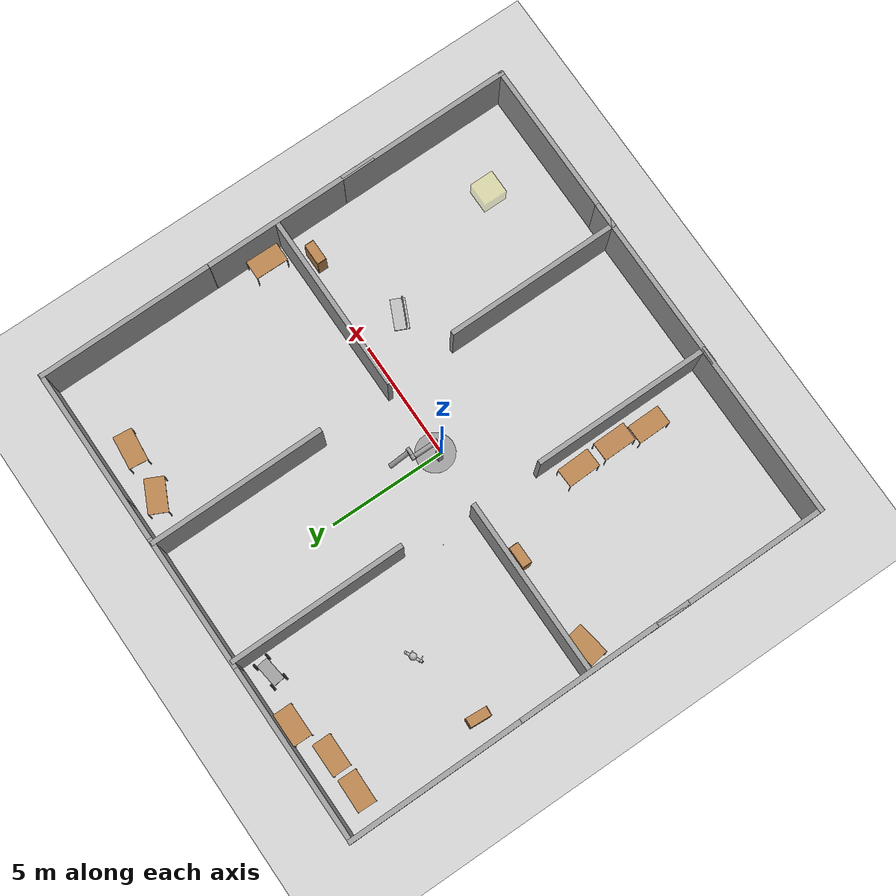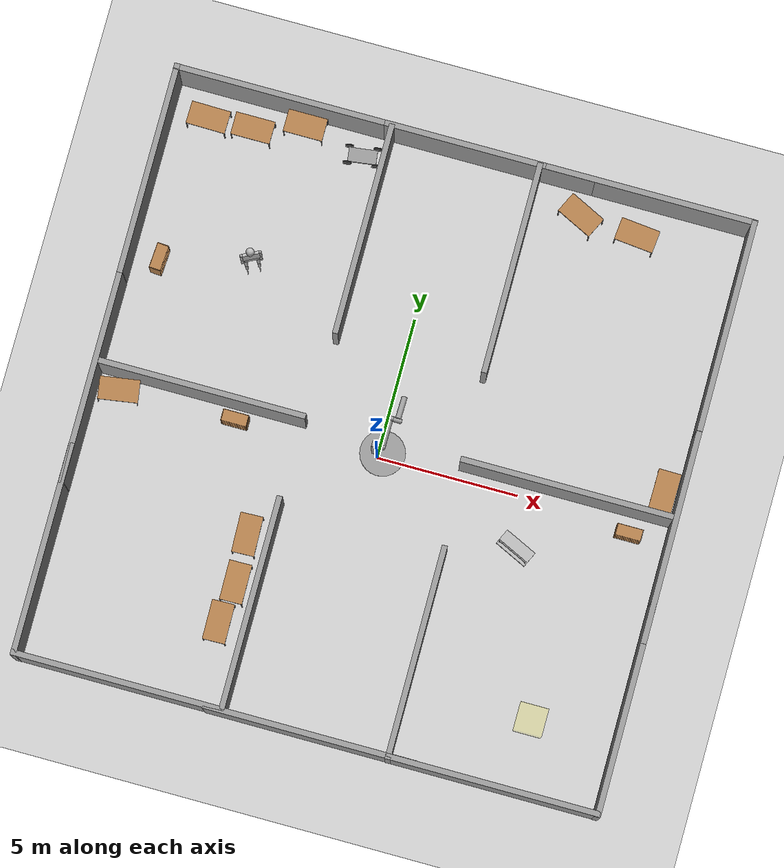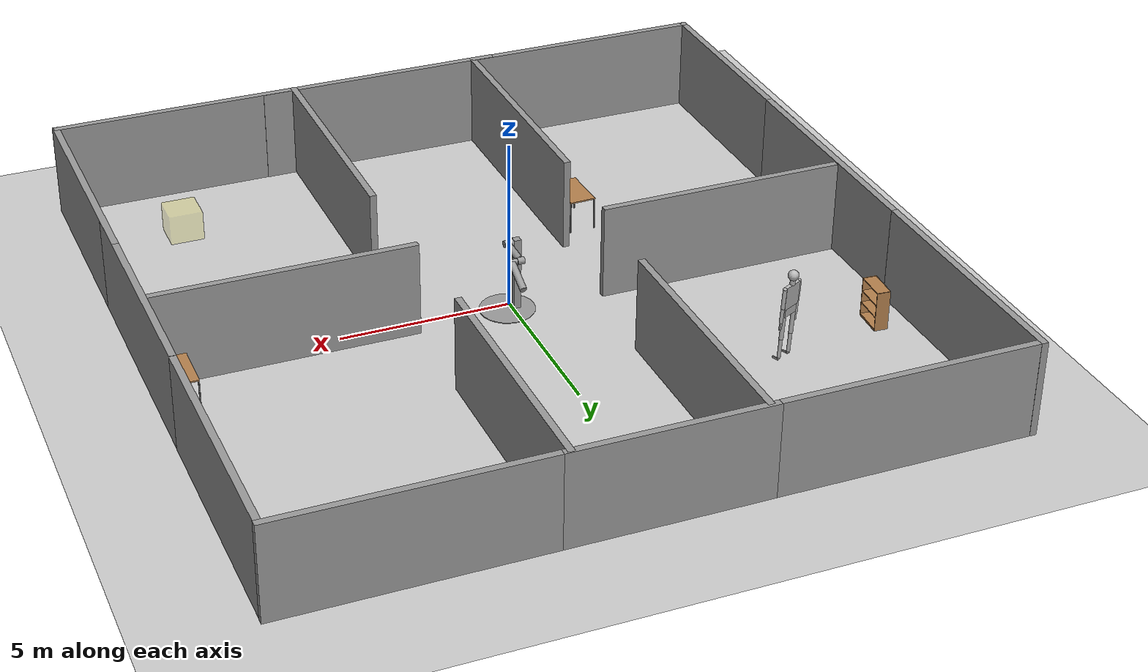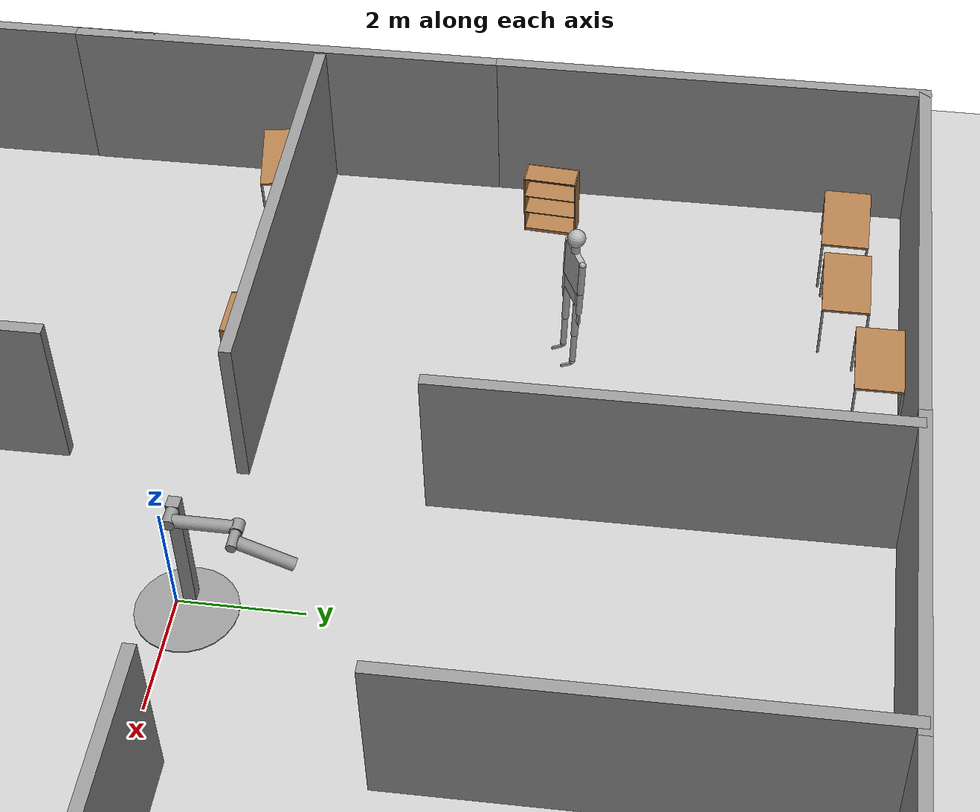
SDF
<sdf version="1.6">
 <world name="default">
  <light name="sun" type="directional">
   <pose>0 0 10 0 -0 0</pose>
   <diffuse>0.8 0.8 0.8 1</diffuse>
   <specular>0.1 0.1 0.1 1</specular>
   <attenuation>
    <range>1000</range>
    <constant>0.9</constant>
    <linear>0.01</linear>
    <quadratic>0.001</quadratic>
   </attenuation>
   <direction>-0.5 0.5 -1</direction>
  </light>
  <model name="ground_plane">
   <static>1</static>
   <link name="link">
    <collision name="collision">
     <geometry><plane><normal>0 0 1</normal><size>100 100</size></plane></geometry>
     <surface><friction><ode><mu>100</mu><mu2>50</mu2></ode></friction></surface>
    </collision>
    <visual name="visual">
     <cast_shadows>0</cast_shadows>
     <geometry><plane><normal>0 0 1</normal><size>100 100</size></plane></geometry>
     <material>
      <script><uri>file://media/materials/scripts/gazebo.material</uri><name>Gazebo/Grey</name></script>
     </material>
    </visual>
   </link>
  </model>
  <gravity>0 0 -9.8</gravity>
  <magnetic_field>6e-06 2.3e-05 -4.2e-05</magnetic_field>
  <atmosphere type="adiabatic"/>
  <physics name="default_physics" default="0" type="ode">
   <max_step_size>0.001</max_step_size>
   <real_time_factor>1</real_time_factor>
   <real_time_update_rate>1000</real_time_update_rate>
  </physics>
  <scene><ambient>0.4 0.4 0.4 1</ambient><background>0.7 0.7 0.7 1</background><shadows>1</shadows></scene>
  <spherical_coordinates>
   <surface_model>EARTH_WGS84</surface_model>
   <latitude_deg>0</latitude_deg>
   <longitude_deg>0</longitude_deg>
   <elevation>0</elevation>
   <heading_deg>0</heading_deg>
  </spherical_coordinates>
  <model name="grey_wall">
   <static>1</static>
   <link name="link">
    <pose>0 0 1.4 0 -0 0</pose>
    <collision name="collision"><geometry><box><size>7.5 0.2 2.8</size></box></geometry></collision>
    <visual name="visual">
     <cast_shadows>0</cast_shadows>
     <geometry><box><size>7.5 0.2 2.8</size></box></geometry>
     <material>
      <script>
       <uri>model://grey_wall/materials/scripts</uri>
       <uri>model://grey_wall/materials/textures</uri>
       <name>vrc/grey_wall</name>
      </script>
     </material>
    </visual>
   </link>
   <pose>-6.47613 10.9124 0 0 -0 0</pose>
  </model>
  <model name="grey_wall_clone">
   <static>1</static>
   <link name="link">
    <pose>0 0 1.4 0 -0 0</pose>
    <collision name="collision"><geometry><box><size>7.5 0.2 2.8</size></box></geometry></collision>
    <visual name="visual">
     <cast_shadows>0</cast_shadows>
     <geometry><box><size>7.5 0.2 2.8</size></box></geometry>
     <material>
      <script>
       <uri>model://grey_wall/materials/scripts</uri>
       <uri>model://grey_wall/materials/textures</uri>
       <name>vrc/grey_wall</name>
      </script>
     </material>
    </visual>
   </link>
   <pose>1.00661 10.9168 -0.00011 0 -0 0</pose>
  </model>
  <model name="grey_wall_clone_0">
   <static>1</static>
   <link name="link">
    <pose>0 0 1.4 0 -0 0</pose>
    <collision name="collision"><geometry><box><size>7.5 0.2 2.8</size></box></geometry></collision>
    <visual name="visual">
     <cast_shadows>0</cast_shadows>
     <geometry><box><size>7.5 0.2 2.8</size></box></geometry>
     <material>
      <script>
       <uri>model://grey_wall/materials/scripts</uri>
       <uri>model://grey_wall/materials/textures</uri>
       <name>vrc/grey_wall</name>
      </script>
     </material>
    </visual>
   </link>
   <pose>6.74015 10.9183 0 0 -0 0</pose>
  </model>
  <model name="grey_wall_0">
   <static>1</static>
   <link name="link">
    <pose>0 0 1.4 0 -0 0</pose>
    <collision name="collision"><geometry><box><size>7.5 0.2 2.8</size></box></geometry></collision>
    <visual name="visual">
     <cast_shadows>0</cast_shadows>
     <geometry><box><size>7.5 0.2 2.8</size></box></geometry>
     <material>
      <script>
       <uri>model://grey_wall/materials/scripts</uri>
       <uri>model://grey_wall/materials/textures</uri>
       <name>vrc/grey_wall</name>
      </script>
     </material>
    </visual>
   </link>
   <pose>-6.3811 -9.93831 0 0 -0 0</pose>
  </model>
  <model name="grey_wall_clone_1">
   <static>1</static>
   <link name="link">
    <pose>0 0 1.4 0 -0 0</pose>
    <collision name="collision"><geometry><box><size>7.5 0.2 2.8</size></box></geometry></collision>
    <visual name="visual">
     <cast_shadows>0</cast_shadows>
     <geometry><box><size>7.5 0.2 2.8</size></box></geometry>
     <material>
      <script>
       <uri>model://grey_wall/materials/scripts</uri>
       <uri>model://grey_wall/materials/textures</uri>
       <name>vrc/grey_wall</name>
      </script>
     </material>
    </visual>
   </link>
   <pose>-10.106 7.26818 0 0 0 -1.56602</pose>
  </model>
  <model name="grey_wall_clone_1_clone">
   <static>1</static>
   <link name="link">
    <pose>0 0 1.4 0 -0 0</pose>
    <collision name="collision"><geometry><box><size>7.5 0.2 2.8</size></box></geometry></collision>
    <visual name="visual">
     <cast_shadows>0</cast_shadows>
     <geometry><box><size>7.5 0.2 2.8</size></box></geometry>
     <material>
      <script>
       <uri>model://grey_wall/materials/scripts</uri>
       <uri>model://grey_wall/materials/textures</uri>
       <name>vrc/grey_wall</name>
      </script>
     </material>
    </visual>
   </link>
   <pose>-10.0659 -0.208527 0 0 0 -1.56602</pose>
  </model>
  <model name="grey_wall_clone_1_clone_clone">
   <static>1</static>
   <link name="link">
    <pose>0 0 1.4 0 -0 0</pose>
    <collision name="collision"><geometry><box><size>7.5 0.2 2.8</size></box></geometry></collision>
    <visual name="visual">
     <cast_shadows>0</cast_shadows>
     <geometry><box><size>7.5 0.2 2.8</size></box></geometry>
     <material>
      <script>
       <uri>model://grey_wall/materials/scripts</uri>
       <uri>model://grey_wall/materials/textures</uri>
       <name>vrc/grey_wall</name>
      </script>
     </material>
    </visual>
   </link>
   <pose>-10.0445 -6.29465 0 0 0 -1.56602</pose>
  </model>
  <model name="grey_wall_0_clone">
   <static>1</static>
   <link name="link">
    <pose>0 0 1.4 0 -0 0</pose>
    <collision name="collision"><geometry><box><size>7.5 0.2 2.8</size></box></geometry></collision>
    <visual name="visual">
     <cast_shadows>0</cast_shadows>
     <geometry><box><size>7.5 0.2 2.8</size></box></geometry>
     <material>
      <script>
       <uri>model://grey_wall/materials/scripts</uri>
       <uri>model://grey_wall/materials/textures</uri>
       <name>vrc/grey_wall</name>
      </script>
     </material>
    </visual>
   </link>
   <pose>6.79056 -9.96838 0 0 -0 0</pose>
  </model>
  <model name="grey_wall_clone_1_clone_0">
   <static>1</static>
   <link name="link">
    <pose>0 0 1.4 0 -0 0</pose>
    <collision name="collision"><geometry><box><size>7.5 0.2 2.8</size></box></geometry></collision>
    <visual name="visual">
     <cast_shadows>0</cast_shadows>
     <geometry><box><size>7.5 0.2 2.8</size></box></geometry>
     <material>
      <script>
       <uri>model://grey_wall/materials/scripts</uri>
       <uri>model://grey_wall/materials/textures</uri>
       <name>vrc/grey_wall</name>
      </script>
     </material>
    </visual>
   </link>
   <pose>10.4003 7.24302 0 0 0 -1.56602</pose>
  </model>
  <model name="grey_wall_clone_1_clone_0_clone">
   <static>1</static>
   <link name="link">
    <pose>0 0 1.4 0 -0 0</pose>
    <collision name="collision"><geometry><box><size>7.5 0.2 2.8</size></box></geometry></collision>
    <visual name="visual">
     <cast_shadows>0</cast_shadows>
     <geometry><box><size>7.5 0.2 2.8</size></box></geometry>
     <material>
      <script>
       <uri>model://grey_wall/materials/scripts</uri>
       <uri>model://grey_wall/materials/textures</uri>
       <name>vrc/grey_wall</name>
      </script>
     </material>
    </visual>
   </link>
   <pose>10.4306 -0.266004 0 0 0 -1.56602</pose>
  </model>
  <model name="grey_wall_clone_1_clone_0_clone_0">
   <static>1</static>
   <link name="link">
    <pose>0 0 1.4 0 -0 0</pose>
    <collision name="collision"><geometry><box><size>7.5 0.2 2.8</size></box></geometry></collision>
    <visual name="visual">
     <cast_shadows>0</cast_shadows>
     <geometry><box><size>7.5 0.2 2.8</size></box></geometry>
     <material>
      <script>
       <uri>model://grey_wall/materials/scripts</uri>
       <uri>model://grey_wall/materials/textures</uri>
       <name>vrc/grey_wall</name>
      </script>
     </material>
    </visual>
   </link>
   <pose>10.4587 -6.32755 0 0 0 -1.56602</pose>
  </model>
  <model name="grey_wall_clone_1_clone_0_clone_1">
   <static>1</static>
   <link name="link">
    <pose>0 0 1.4 0 -0 0</pose>
    <collision name="collision"><geometry><box><size>7.5 0.2 2.8</size></box></geometry></collision>
    <visual name="visual">
     <cast_shadows>0</cast_shadows>
     <geometry><box><size>7.5 0.2 2.8</size></box></geometry>
     <material>
      <script>
       <uri>model://grey_wall/materials/scripts</uri>
       <uri>model://grey_wall/materials/textures</uri>
       <name>vrc/grey_wall</name>
      </script>
     </material>
    </visual>
   </link>
   <pose>-2.44809 7.18884 0 0 0 -1.56602</pose>
  </model>
  <model name="grey_wall_clone_2">
   <static>1</static>
   <link name="link">
    <pose>0 0 1.4 0 -0 0</pose>
    <collision name="collision"><geometry><box><size>7.5 0.2 2.8</size></box></geometry></collision>
    <visual name="visual">
     <cast_shadows>0</cast_shadows>
     <geometry><box><size>7.5 0.2 2.8</size></box></geometry>
     <material>
      <script>
       <uri>model://grey_wall/materials/scripts</uri>
       <uri>model://grey_wall/materials/textures</uri>
       <name>vrc/grey_wall</name>
      </script>
     </material>
    </visual>
   </link>
   <pose>-6.38709 0.430449 -0.0279 0 -0 0</pose>
  </model>
  <model name="grey_wall_clone_3">
   <static>1</static>
   <link name="link">
    <pose>0 0 1.4 0 -0 0</pose>
    <collision name="collision"><geometry><box><size>7.5 0.2 2.8</size></box></geometry></collision>
    <visual name="visual">
     <cast_shadows>0</cast_shadows>
     <geometry><box><size>7.5 0.2 2.8</size></box></geometry>
     <material>
      <script>
       <uri>model://grey_wall/materials/scripts</uri>
       <uri>model://grey_wall/materials/textures</uri>
       <name>vrc/grey_wall</name>
      </script>
     </material>
    </visual>
   </link>
   <pose>6.57612 0.423406 0 0 -0 0</pose>
  </model>
  <model name="grey_wall_clone_1_clone_0_clone_1_clone">
   <static>1</static>
   <link name="link">
    <pose>0 0 1.4 0 -0 0</pose>
    <collision name="collision"><geometry><box><size>7.5 0.2 2.8</size></box></geometry></collision>
    <visual name="visual">
     <cast_shadows>0</cast_shadows>
     <geometry><box><size>7.5 0.2 2.8</size></box></geometry>
     <material>
      <script>
       <uri>model://grey_wall/materials/scripts</uri>
       <uri>model://grey_wall/materials/textures</uri>
       <name>vrc/grey_wall</name>
      </script>
     </material>
    </visual>
   </link>
   <pose>2.80527 7.23087 0 0 0 -1.56602</pose>
  </model>
  <model name="grey_wall_clone_1_clone_0_clone_1_clone_clone">
   <static>1</static>
   <link name="link">
    <pose>0 0 1.4 0 -0 0</pose>
    <collision name="collision"><geometry><box><size>7.5 0.2 2.8</size></box></geometry></collision>
    <visual name="visual">
     <cast_shadows>0</cast_shadows>
     <geometry><box><size>7.5 0.2 2.8</size></box></geometry>
     <material>
      <script>
       <uri>model://grey_wall/materials/scripts</uri>
       <uri>model://grey_wall/materials/textures</uri>
       <name>vrc/grey_wall</name>
      </script>
     </material>
    </visual>
   </link>
   <pose>3.11102 -6.32182 0 0 0 -1.56602</pose>
  </model>
  <model name="grey_wall_clone_1_clone_0_clone_1_clone_clone_0">
   <static>1</static>
   <link name="link">
    <pose>0 0 1.4 0 -0 0</pose>
    <collision name="collision"><geometry><box><size>7.5 0.2 2.8</size></box></geometry></collision>
    <visual name="visual">
     <cast_shadows>0</cast_shadows>
     <geometry><box><size>7.5 0.2 2.8</size></box></geometry>
     <material>
      <script>
       <uri>model://grey_wall/materials/scripts</uri>
       <uri>model://grey_wall/materials/textures</uri>
       <name>vrc/grey_wall</name>
      </script>
     </material>
    </visual>
   </link>
   <pose>-2.7422 -6.17524 0 0 0 -1.56602</pose>
  </model>
  <model name="table">
   <static>0</static>
   <link name="link">
    <collision name="surface">
     <pose>0 0 1 0 -0 0</pose>
     <geometry><box><size>1.5 0.8 0.03</size></box></geometry>
     <surface><friction><ode><mu>0.6</mu><mu2>0.6</mu2></ode></friction></surface>
    </collision>
    <visual name="visual1">
     <pose>0 0 1 0 -0 0</pose>
     <geometry><box><size>1.4 0.8 0.04</size></box></geometry>
     <material>
      <script><uri>file://media/materials/scripts/gazebo.material</uri><name>Gazebo/Wood</name></script>
     </material>
    </visual>
    <collision name="front_left_leg">
     <pose>0.68 0.38 0.5 0 -0 0</pose>
     <geometry><cylinder><radius>0.02</radius><length>1</length></cylinder></geometry>
    </collision>
    <visual name="front_left_leg">
     <pose>0.68 0.38 0.5 0 -0 0</pose>
     <geometry><cylinder><radius>0.02</radius><length>1</length></cylinder></geometry>
     <material>
      <script><uri>file://media/materials/scripts/gazebo.material</uri><name>Gazebo/Grey</name></script>
     </material>
    </visual>
    <collision name="front_right_leg">
     <pose>0.68 -0.38 0.5 0 -0 0</pose>
     <geometry><cylinder><radius>0.02</radius><length>1</length></cylinder></geometry>
    </collision>
    <visual name="front_right_leg">
     <pose>0.68 -0.38 0.5 0 -0 0</pose>
     <geometry><cylinder><radius>0.02</radius><length>1</length></cylinder></geometry>
     <material>
      <script><uri>file://media/materials/scripts/gazebo.material</uri><name>Gazebo/Grey</name></script>
     </material>
    </visual>
    <collision name="back_right_leg">
     <pose>-0.68 -0.38 0.5 0 -0 0</pose>
     <geometry><cylinder><radius>0.02</radius><length>1</length></cylinder></geometry>
    </collision>
    <visual name="back_right_leg">
     <pose>-0.68 -0.38 0.5 0 -0 0</pose>
     <geometry><cylinder><radius>0.02</radius><length>1</length></cylinder></geometry>
     <material>
      <script><uri>file://media/materials/scripts/gazebo.material</uri><name>Gazebo/Grey</name></script>
     </material>
    </visual>
    <collision name="back_left_leg">
     <pose>-0.68 0.38 0.5 0 -0 0</pose>
     <geometry><cylinder><radius>0.02</radius><length>1</length></cylinder></geometry>
    </collision>
    <visual name="back_left_leg">
     <pose>-0.68 0.38 0.5 0 -0 0</pose>
     <geometry><cylinder><radius>0.02</radius><length>1</length></cylinder></geometry>
     <material>
      <script><uri>file://media/materials/scripts/gazebo.material</uri><name>Gazebo/Grey</name></script>
     </material>
    </visual>
    <inertial>
     <inertia><ixx>1</ixx><ixy>0</ixy><ixz>0</ixz><iyy>1</iyy><iyz>0</iyz><izz>1</izz></inertia>
     <mass>1</mass>
    </inertial>
   </link>
   <pose>-9.21004 -0.177966 0.035504 0.011453 0.044483 0.156844</pose>
  </model>
  <model name="table_clone">
   <static>0</static>
   <link name="link">
    <collision name="surface">
     <pose>0 0 1 0 -0 0</pose>
     <geometry><box><size>1.5 0.8 0.03</size></box></geometry>
     <surface><friction><ode><mu>0.6</mu><mu2>0.6</mu2></ode></friction></surface>
    </collision>
    <visual name="visual1">
     <pose>0 0 1 0 -0 0</pose>
     <geometry><box><size>1.4 0.8 0.04</size></box></geometry>
     <material>
      <script><uri>file://media/materials/scripts/gazebo.material</uri><name>Gazebo/Wood</name></script>
     </material>
    </visual>
    <collision name="front_left_leg">
     <pose>0.68 0.38 0.5 0 -0 0</pose>
     <geometry><cylinder><radius>0.02</radius><length>1</length></cylinder></geometry>
    </collision>
    <visual name="front_left_leg">
     <pose>0.68 0.38 0.5 0 -0 0</pose>
     <geometry><cylinder><radius>0.02</radius><length>1</length></cylinder></geometry>
     <material>
      <script><uri>file://media/materials/scripts/gazebo.material</uri><name>Gazebo/Grey</name></script>
     </material>
    </visual>
    <collision name="front_right_leg">
     <pose>0.68 -0.38 0.5 0 -0 0</pose>
     <geometry><cylinder><radius>0.02</radius><length>1</length></cylinder></geometry>
    </collision>
    <visual name="front_right_leg">
     <pose>0.68 -0.38 0.5 0 -0 0</pose>
     <geometry><cylinder><radius>0.02</radius><length>1</length></cylinder></geometry>
     <material>
      <script><uri>file://media/materials/scripts/gazebo.material</uri><name>Gazebo/Grey</name></script>
     </material>
    </visual>
    <collision name="back_right_leg">
     <pose>-0.68 -0.38 0.5 0 -0 0</pose>
     <geometry><cylinder><radius>0.02</radius><length>1</length></cylinder></geometry>
    </collision>
    <visual name="back_right_leg">
     <pose>-0.68 -0.38 0.5 0 -0 0</pose>
     <geometry><cylinder><radius>0.02</radius><length>1</length></cylinder></geometry>
     <material>
      <script><uri>file://media/materials/scripts/gazebo.material</uri><name>Gazebo/Grey</name></script>
     </material>
    </visual>
    <collision name="back_left_leg">
     <pose>-0.68 0.38 0.5 0 -0 0</pose>
     <geometry><cylinder><radius>0.02</radius><length>1</length></cylinder></geometry>
    </collision>
    <visual name="back_left_leg">
     <pose>-0.68 0.38 0.5 0 -0 0</pose>
     <geometry><cylinder><radius>0.02</radius><length>1</length></cylinder></geometry>
     <material>
      <script><uri>file://media/materials/scripts/gazebo.material</uri><name>Gazebo/Grey</name></script>
     </material>
    </visual>
    <inertial>
     <inertia><ixx>1</ixx><ixy>0</ixy><ixz>0</ixz><iyy>1</iyy><iyz>0</iyz><izz>1</izz></inertia>
     <mass>1</mass>
    </inertial>
   </link>
   <pose>-3.56323 -3.82904 -9e-06 0 1e-06 1.60529</pose>
  </model>
  <model name="table_clone_3">
   <static>0</static>
   <link name="link">
    <collision name="surface">
     <pose>0 0 1 0 -0 0</pose>
     <geometry><box><size>1.5 0.8 0.03</size></box></geometry>
     <surface><friction><ode><mu>0.6</mu><mu2>0.6</mu2></ode></friction></surface>
    </collision>
    <visual name="visual1">
     <pose>0 0 1 0 -0 0</pose>
     <geometry><box><size>1.4 0.8 0.04</size></box></geometry>
     <material>
      <script><uri>file://media/materials/scripts/gazebo.material</uri><name>Gazebo/Wood</name></script>
     </material>
    </visual>
    <collision name="front_left_leg">
     <pose>0.68 0.38 0.5 0 -0 0</pose>
     <geometry><cylinder><radius>0.02</radius><length>1</length></cylinder></geometry>
    </collision>
    <visual name="front_left_leg">
     <pose>0.68 0.38 0.5 0 -0 0</pose>
     <geometry><cylinder><radius>0.02</radius><length>1</length></cylinder></geometry>
     <material>
      <script><uri>file://media/materials/scripts/gazebo.material</uri><name>Gazebo/Grey</name></script>
     </material>
    </visual>
    <collision name="front_right_leg">
     <pose>0.68 -0.38 0.5 0 -0 0</pose>
     <geometry><cylinder><radius>0.02</radius><length>1</length></cylinder></geometry>
    </collision>
    <visual name="front_right_leg">
     <pose>0.68 -0.38 0.5 0 -0 0</pose>
     <geometry><cylinder><radius>0.02</radius><length>1</length></cylinder></geometry>
     <material>
      <script><uri>file://media/materials/scripts/gazebo.material</uri><name>Gazebo/Grey</name></script>
     </material>
    </visual>
    <collision name="back_right_leg">
     <pose>-0.68 -0.38 0.5 0 -0 0</pose>
     <geometry><cylinder><radius>0.02</radius><length>1</length></cylinder></geometry>
    </collision>
    <visual name="back_right_leg">
     <pose>-0.68 -0.38 0.5 0 -0 0</pose>
     <geometry><cylinder><radius>0.02</radius><length>1</length></cylinder></geometry>
     <material>
      <script><uri>file://media/materials/scripts/gazebo.material</uri><name>Gazebo/Grey</name></script>
     </material>
    </visual>
    <collision name="back_left_leg">
     <pose>-0.68 0.38 0.5 0 -0 0</pose>
     <geometry><cylinder><radius>0.02</radius><length>1</length></cylinder></geometry>
    </collision>
    <visual name="back_left_leg">
     <pose>-0.68 0.38 0.5 0 -0 0</pose>
     <geometry><cylinder><radius>0.02</radius><length>1</length></cylinder></geometry>
     <material>
      <script><uri>file://media/materials/scripts/gazebo.material</uri><name>Gazebo/Grey</name></script>
     </material>
    </visual>
    <inertial>
     <inertia><ixx>1</ixx><ixy>0</ixy><ixz>0</ixz><iyy>1</iyy><iyz>0</iyz><izz>1</izz></inertia>
     <mass>1</mass>
    </inertial>
   </link>
   <pose>9.86597 1.39822 -2e-06 0 0 -1.58101</pose>
  </model>
  <model name="table_clone_4">
   <static>0</static>
   <link name="link">
    <collision name="surface">
     <pose>0 0 1 0 -0 0</pose>
     <geometry><box><size>1.5 0.8 0.03</size></box></geometry>
     <surface><friction><ode><mu>0.6</mu><mu2>0.6</mu2></ode></friction></surface>
    </collision>
    <visual name="visual1">
     <pose>0 0 1 0 -0 0</pose>
     <geometry><box><size>1.4 0.8 0.04</size></box></geometry>
     <material>
      <script><uri>file://media/materials/scripts/gazebo.material</uri><name>Gazebo/Wood</name></script>
     </material>
    </visual>
    <collision name="front_left_leg">
     <pose>0.68 0.38 0.5 0 -0 0</pose>
     <geometry><cylinder><radius>0.02</radius><length>1</length></cylinder></geometry>
    </collision>
    <visual name="front_left_leg">
     <pose>0.68 0.38 0.5 0 -0 0</pose>
     <geometry><cylinder><radius>0.02</radius><length>1</length></cylinder></geometry>
     <material>
      <script><uri>file://media/materials/scripts/gazebo.material</uri><name>Gazebo/Grey</name></script>
     </material>
    </visual>
    <collision name="front_right_leg">
     <pose>0.68 -0.38 0.5 0 -0 0</pose>
     <geometry><cylinder><radius>0.02</radius><length>1</length></cylinder></geometry>
    </collision>
    <visual name="front_right_leg">
     <pose>0.68 -0.38 0.5 0 -0 0</pose>
     <geometry><cylinder><radius>0.02</radius><length>1</length></cylinder></geometry>
     <material>
      <script><uri>file://media/materials/scripts/gazebo.material</uri><name>Gazebo/Grey</name></script>
     </material>
    </visual>
    <collision name="back_right_leg">
     <pose>-0.68 -0.38 0.5 0 -0 0</pose>
     <geometry><cylinder><radius>0.02</radius><length>1</length></cylinder></geometry>
    </collision>
    <visual name="back_right_leg">
     <pose>-0.68 -0.38 0.5 0 -0 0</pose>
     <geometry><cylinder><radius>0.02</radius><length>1</length></cylinder></geometry>
     <material>
      <script><uri>file://media/materials/scripts/gazebo.material</uri><name>Gazebo/Grey</name></script>
     </material>
    </visual>
    <collision name="back_left_leg">
     <pose>-0.68 0.38 0.5 0 -0 0</pose>
     <geometry><cylinder><radius>0.02</radius><length>1</length></cylinder></geometry>
    </collision>
    <visual name="back_left_leg">
     <pose>-0.68 0.38 0.5 0 -0 0</pose>
     <geometry><cylinder><radius>0.02</radius><length>1</length></cylinder></geometry>
     <material>
      <script><uri>file://media/materials/scripts/gazebo.material</uri><name>Gazebo/Grey</name></script>
     </material>
    </visual>
    <inertial>
     <inertia><ixx>1</ixx><ixy>0</ixy><ixz>0</ixz><iyy>1</iyy><iyz>0</iyz><izz>1</izz></inertia>
     <mass>1</mass>
    </inertial>
   </link>
   <pose>4.58626 9.89882 -1e-06 -1e-06 -1e-06 -0.451145</pose>
  </model>
  <model name="table_clone_5">
   <static>0</static>
   <link name="link">
    <collision name="surface">
     <pose>0 0 1 0 -0 0</pose>
     <geometry><box><size>1.5 0.8 0.03</size></box></geometry>
     <surface><friction><ode><mu>0.6</mu><mu2>0.6</mu2></ode></friction></surface>
    </collision>
    <visual name="visual1">
     <pose>0 0 1 0 -0 0</pose>
     <geometry><box><size>1.4 0.8 0.04</size></box></geometry>
     <material>
      <script><uri>file://media/materials/scripts/gazebo.material</uri><name>Gazebo/Wood</name></script>
     </material>
    </visual>
    <collision name="front_left_leg">
     <pose>0.68 0.38 0.5 0 -0 0</pose>
     <geometry><cylinder><radius>0.02</radius><length>1</length></cylinder></geometry>
    </collision>
    <visual name="front_left_leg">
     <pose>0.68 0.38 0.5 0 -0 0</pose>
     <geometry><cylinder><radius>0.02</radius><length>1</length></cylinder></geometry>
     <material>
      <script><uri>file://media/materials/scripts/gazebo.material</uri><name>Gazebo/Grey</name></script>
     </material>
    </visual>
    <collision name="front_right_leg">
     <pose>0.68 -0.38 0.5 0 -0 0</pose>
     <geometry><cylinder><radius>0.02</radius><length>1</length></cylinder></geometry>
    </collision>
    <visual name="front_right_leg">
     <pose>0.68 -0.38 0.5 0 -0 0</pose>
     <geometry><cylinder><radius>0.02</radius><length>1</length></cylinder></geometry>
     <material>
      <script><uri>file://media/materials/scripts/gazebo.material</uri><name>Gazebo/Grey</name></script>
     </material>
    </visual>
    <collision name="back_right_leg">
     <pose>-0.68 -0.38 0.5 0 -0 0</pose>
     <geometry><cylinder><radius>0.02</radius><length>1</length></cylinder></geometry>
    </collision>
    <visual name="back_right_leg">
     <pose>-0.68 -0.38 0.5 0 -0 0</pose>
     <geometry><cylinder><radius>0.02</radius><length>1</length></cylinder></geometry>
     <material>
      <script><uri>file://media/materials/scripts/gazebo.material</uri><name>Gazebo/Grey</name></script>
     </material>
    </visual>
    <collision name="back_left_leg">
     <pose>-0.68 0.38 0.5 0 -0 0</pose>
     <geometry><cylinder><radius>0.02</radius><length>1</length></cylinder></geometry>
    </collision>
    <visual name="back_left_leg">
     <pose>-0.68 0.38 0.5 0 -0 0</pose>
     <geometry><cylinder><radius>0.02</radius><length>1</length></cylinder></geometry>
     <material>
      <script><uri>file://media/materials/scripts/gazebo.material</uri><name>Gazebo/Grey</name></script>
     </material>
    </visual>
    <inertial>
     <inertia><ixx>1</ixx><ixy>0</ixy><ixz>0</ixz><iyy>1</iyy><iyz>0</iyz><izz>1</izz></inertia>
     <mass>1</mass>
    </inertial>
   </link>
   <pose>6.64272 9.72922 -9e-06 0 -1e-06 -0.101108</pose>
  </model>
  <model name="table_clone_clone">
   <static>0</static>
   <link name="link">
    <collision name="surface">
     <pose>0 0 1 0 -0 0</pose>
     <geometry><box><size>1.5 0.8 0.03</size></box></geometry>
     <surface><friction><ode><mu>0.6</mu><mu2>0.6</mu2></ode></friction></surface>
    </collision>
    <visual name="visual1">
     <pose>0 0 1 0 -0 0</pose>
     <geometry><box><size>1.4 0.8 0.04</size></box></geometry>
     <material>
      <script><uri>file://media/materials/scripts/gazebo.material</uri><name>Gazebo/Wood</name></script>
     </material>
    </visual>
    <collision name="front_left_leg">
     <pose>0.68 0.38 0.5 0 -0 0</pose>
     <geometry><cylinder><radius>0.02</radius><length>1</length></cylinder></geometry>
    </collision>
    <visual name="front_left_leg">
     <pose>0.68 0.38 0.5 0 -0 0</pose>
     <geometry><cylinder><radius>0.02</radius><length>1</length></cylinder></geometry>
     <material>
      <script><uri>file://media/materials/scripts/gazebo.material</uri><name>Gazebo/Grey</name></script>
     </material>
    </visual>
    <collision name="front_right_leg">
     <pose>0.68 -0.38 0.5 0 -0 0</pose>
     <geometry><cylinder><radius>0.02</radius><length>1</length></cylinder></geometry>
    </collision>
    <visual name="front_right_leg">
     <pose>0.68 -0.38 0.5 0 -0 0</pose>
     <geometry><cylinder><radius>0.02</radius><length>1</length></cylinder></geometry>
     <material>
      <script><uri>file://media/materials/scripts/gazebo.material</uri><name>Gazebo/Grey</name></script>
     </material>
    </visual>
    <collision name="back_right_leg">
     <pose>-0.68 -0.38 0.5 0 -0 0</pose>
     <geometry><cylinder><radius>0.02</radius><length>1</length></cylinder></geometry>
    </collision>
    <visual name="back_right_leg">
     <pose>-0.68 -0.38 0.5 0 -0 0</pose>
     <geometry><cylinder><radius>0.02</radius><length>1</length></cylinder></geometry>
     <material>
      <script><uri>file://media/materials/scripts/gazebo.material</uri><name>Gazebo/Grey</name></script>
     </material>
    </visual>
    <collision name="back_left_leg">
     <pose>-0.68 0.38 0.5 0 -0 0</pose>
     <geometry><cylinder><radius>0.02</radius><length>1</length></cylinder></geometry>
    </collision>
    <visual name="back_left_leg">
     <pose>-0.68 0.38 0.5 0 -0 0</pose>
     <geometry><cylinder><radius>0.02</radius><length>1</length></cylinder></geometry>
     <material>
      <script><uri>file://media/materials/scripts/gazebo.material</uri><name>Gazebo/Grey</name></script>
     </material>
    </visual>
    <inertial>
     <inertia><ixx>1</ixx><ixy>0</ixy><ixz>0</ixz><iyy>1</iyy><iyz>0</iyz><izz>1</izz></inertia>
     <mass>1</mass>
    </inertial>
   </link>
   <pose>-3.50674 -5.54427 0.015018 -1e-06 0.021456 1.58732</pose>
  </model>
  <model name="table_clone_clone_0">
   <static>0</static>
   <link name="link">
    <collision name="surface">
     <pose>0 0 1 0 -0 0</pose>
     <geometry><box><size>1.5 0.8 0.03</size></box></geometry>
     <surface><friction><ode><mu>0.6</mu><mu2>0.6</mu2></ode></friction></surface>
    </collision>
    <visual name="visual1">
     <pose>0 0 1 0 -0 0</pose>
     <geometry><box><size>1.4 0.8 0.04</size></box></geometry>
     <material>
      <script><uri>file://media/materials/scripts/gazebo.material</uri><name>Gazebo/Wood</name></script>
     </material>
    </visual>
    <collision name="front_left_leg">
     <pose>0.68 0.38 0.5 0 -0 0</pose>
     <geometry><cylinder><radius>0.02</radius><length>1</length></cylinder></geometry>
    </collision>
    <visual name="front_left_leg">
     <pose>0.68 0.38 0.5 0 -0 0</pose>
     <geometry><cylinder><radius>0.02</radius><length>1</length></cylinder></geometry>
     <material>
      <script><uri>file://media/materials/scripts/gazebo.material</uri><name>Gazebo/Grey</name></script>
     </material>
    </visual>
    <collision name="front_right_leg">
     <pose>0.68 -0.38 0.5 0 -0 0</pose>
     <geometry><cylinder><radius>0.02</radius><length>1</length></cylinder></geometry>
    </collision>
    <visual name="front_right_leg">
     <pose>0.68 -0.38 0.5 0 -0 0</pose>
     <geometry><cylinder><radius>0.02</radius><length>1</length></cylinder></geometry>
     <material>
      <script><uri>file://media/materials/scripts/gazebo.material</uri><name>Gazebo/Grey</name></script>
     </material>
    </visual>
    <collision name="back_right_leg">
     <pose>-0.68 -0.38 0.5 0 -0 0</pose>
     <geometry><cylinder><radius>0.02</radius><length>1</length></cylinder></geometry>
    </collision>
    <visual name="back_right_leg">
     <pose>-0.68 -0.38 0.5 0 -0 0</pose>
     <geometry><cylinder><radius>0.02</radius><length>1</length></cylinder></geometry>
     <material>
      <script><uri>file://media/materials/scripts/gazebo.material</uri><name>Gazebo/Grey</name></script>
     </material>
    </visual>
    <collision name="back_left_leg">
     <pose>-0.68 0.38 0.5 0 -0 0</pose>
     <geometry><cylinder><radius>0.02</radius><length>1</length></cylinder></geometry>
    </collision>
    <visual name="back_left_leg">
     <pose>-0.68 0.38 0.5 0 -0 0</pose>
     <geometry><cylinder><radius>0.02</radius><length>1</length></cylinder></geometry>
     <material>
      <script><uri>file://media/materials/scripts/gazebo.material</uri><name>Gazebo/Grey</name></script>
     </material>
    </visual>
    <inertial>
     <inertia><ixx>1</ixx><ixy>0</ixy><ixz>0</ixz><iyy>1</iyy><iyz>0</iyz><izz>1</izz></inertia>
     <mass>1</mass>
    </inertial>
   </link>
   <pose>-3.70915 -6.98496 -1.3e-05 2e-06 0 1.5879</pose>
  </model>
  <model name="grey_wall_0_clone_0">
   <static>1</static>
   <link name="link">
    <pose>0 0 1.4 0 -0 0</pose>
    <collision name="collision"><geometry><box><size>7.5 0.2 2.8</size></box></geometry></collision>
    <visual name="visual">
     <cast_shadows>0</cast_shadows>
     <geometry><box><size>7.5 0.2 2.8</size></box></geometry>
     <material>
      <script>
       <uri>model://grey_wall/materials/scripts</uri>
       <uri>model://grey_wall/materials/textures</uri>
       <name>vrc/grey_wall</name>
      </script>
     </material>
    </visual>
   </link>
   <pose>0.379741 -9.95906 0 0 -0 0</pose>
  </model>
  <model name="cart_front_steer">
   <link name="chassis">
    <pose>0 0 0.15 0 -0 0</pose>
    <inertial>
     <pose>0.1 0 0 0 -0 0</pose>
     <mass>10</mass>
     <inertia>
      <ixx>0.216667</ixx>
      <iyy>0.841667</iyy>
      <izz>1.04167</izz>
      <ixy>0</ixy>
      <ixz>0</ixz>
      <iyz>0</iyz>
     </inertia>
    </inertial>
    <collision name="collision"><geometry><box><size>1 0.5 0.1</size></box></geometry></collision>
    <visual name="visual">
     <geometry><box><size>1 0.5 0.1</size></box></geometry>
     <material>
      <script><uri>file://media/materials/scripts/gazebo.material</uri><name>Gazebo/Grey</name></script>
     </material>
    </visual>
   </link>
   <link name="wheel_front_left">
    <pose>0.5 0.298 0.15 -1.5708 -0.087266 0</pose>
    <inertial>
     <mass>0.5</mass>
     <inertia>
      <ixx>0.00307917</ixx>
      <iyy>0.00307917</iyy>
      <izz>0.005625</izz>
      <ixy>0</ixy>
      <ixz>0</ixz>
      <iyz>0</iyz>
     </inertia>
    </inertial>
    <collision name="collision">
     <geometry><cylinder><radius>0.15</radius><length>0.08</length></cylinder></geometry>
    </collision>
    <visual name="visual">
     <geometry><cylinder><radius>0.15</radius><length>0.08</length></cylinder></geometry>
     <material>
      <script><uri>file://media/materials/scripts/gazebo.material</uri><name>Gazebo/Black</name></script>
     </material>
    </visual>
   </link>
   <joint name="wheel_front_left_steer_spin" type="universal">
    <parent>chassis</parent>
    <child>wheel_front_left</child>
    <axis>
     <xyz>0 -1 0</xyz>
     <limit><lower>-0.610865</lower><upper>0.610865</upper></limit>
     <use_parent_model_frame>0</use_parent_model_frame>
     <dynamics><spring_reference>0</spring_reference><spring_stiffness>0</spring_stiffness></dynamics>
    </axis>
    <axis2>
     <xyz>0 0 1</xyz>
     <use_parent_model_frame>0</use_parent_model_frame>
     <dynamics><spring_reference>0</spring_reference><spring_stiffness>0</spring_stiffness></dynamics>
    </axis2>
   </joint>
   <link name="wheel_front_right">
    <pose>0.5 -0.298 0.15 -1.5708 -0.087266 0</pose>
    <inertial>
     <mass>0.5</mass>
     <inertia>
      <ixx>0.00307917</ixx>
      <iyy>0.00307917</iyy>
      <izz>0.005625</izz>
      <ixy>0</ixy>
      <ixz>0</ixz>
      <iyz>0</iyz>
     </inertia>
    </inertial>
    <collision name="collision">
     <geometry><cylinder><radius>0.15</radius><length>0.08</length></cylinder></geometry>
    </collision>
    <visual name="visual">
     <geometry><cylinder><radius>0.15</radius><length>0.08</length></cylinder></geometry>
     <material>
      <script><uri>file://media/materials/scripts/gazebo.material</uri><name>Gazebo/Black</name></script>
     </material>
    </visual>
   </link>
   <joint name="wheel_front_right_steer_spin" type="universal">
    <parent>chassis</parent>
    <child>wheel_front_right</child>
    <axis>
     <xyz>0 -1 0</xyz>
     <limit><lower>-0.610865</lower><upper>0.610865</upper></limit>
     <use_parent_model_frame>0</use_parent_model_frame>
     <dynamics><spring_reference>0</spring_reference><spring_stiffness>0</spring_stiffness></dynamics>
    </axis>
    <axis2>
     <xyz>0 0 1</xyz>
     <use_parent_model_frame>0</use_parent_model_frame>
     <dynamics><spring_reference>0</spring_reference><spring_stiffness>0</spring_stiffness></dynamics>
    </axis2>
   </joint>
   <link name="wheel_rear_left">
    <pose>-0.5 0.298 0.15 -1.5708 0 0</pose>
    <inertial>
     <mass>0.5</mass>
     <inertia>
      <ixx>0.00307917</ixx>
      <iyy>0.00307917</iyy>
      <izz>0.005625</izz>
      <ixy>0</ixy>
      <ixz>0</ixz>
      <iyz>0</iyz>
     </inertia>
    </inertial>
    <collision name="collision">
     <geometry><cylinder><radius>0.15</radius><length>0.08</length></cylinder></geometry>
    </collision>
    <visual name="visual">
     <geometry><cylinder><radius>0.15</radius><length>0.08</length></cylinder></geometry>
     <material>
      <script><uri>file://media/materials/scripts/gazebo.material</uri><name>Gazebo/Black</name></script>
     </material>
    </visual>
   </link>
   <joint name="wheel_rear_left_spin" type="revolute">
    <parent>chassis</parent>
    <child>wheel_rear_left</child>
    <axis>
     <xyz>0 0 1</xyz>
     <use_parent_model_frame>0</use_parent_model_frame>
     <limit><lower>-1e+16</lower><upper>1e+16</upper></limit>
     <dynamics><spring_reference>0</spring_reference><spring_stiffness>0</spring_stiffness></dynamics>
    </axis>
   </joint>
   <link name="wheel_rear_right">
    <pose>-0.5 -0.298 0.15 -1.5708 0 0</pose>
    <inertial>
     <mass>0.5</mass>
     <inertia>
      <ixx>0.00307917</ixx>
      <iyy>0.00307917</iyy>
      <izz>0.005625</izz>
      <ixy>0</ixy>
      <ixz>0</ixz>
      <iyz>0</iyz>
     </inertia>
    </inertial>
    <collision name="collision">
     <geometry><cylinder><radius>0.15</radius><length>0.08</length></cylinder></geometry>
    </collision>
    <visual name="visual">
     <geometry><cylinder><radius>0.15</radius><length>0.08</length></cylinder></geometry>
     <material>
      <script><uri>file://media/materials/scripts/gazebo.material</uri><name>Gazebo/Black</name></script>
     </material>
    </visual>
   </link>
   <joint name="wheel_rear_right_spin" type="revolute">
    <parent>chassis</parent>
    <child>wheel_rear_right</child>
    <axis>
     <xyz>0 0 1</xyz>
     <use_parent_model_frame>0</use_parent_model_frame>
     <limit><lower>-1e+16</lower><upper>1e+16</upper></limit>
     <dynamics><spring_reference>0</spring_reference><spring_stiffness>0</spring_stiffness></dynamics>
    </axis>
   </joint>
   <pose>-3.2833 10.0314 -8e-06 2.6e-05 -1e-06 0.128649</pose>
  </model>
  <model name="table_clone_0">
   <static>0</static>
   <link name="link">
    <collision name="surface">
     <pose>0 0 1 0 -0 0</pose>
     <geometry><box><size>1.5 0.8 0.03</size></box></geometry>
     <surface><friction><ode><mu>0.6</mu><mu2>0.6</mu2></ode></friction></surface>
    </collision>
    <visual name="visual1">
     <pose>0 0 1 0 -0 0</pose>
     <geometry><box><size>1.4 0.8 0.04</size></box></geometry>
     <material>
      <script><uri>file://media/materials/scripts/gazebo.material</uri><name>Gazebo/Wood</name></script>
     </material>
    </visual>
    <collision name="front_left_leg">
     <pose>0.68 0.38 0.5 0 -0 0</pose>
     <geometry><cylinder><radius>0.02</radius><length>1</length></cylinder></geometry>
    </collision>
    <visual name="front_left_leg">
     <pose>0.68 0.38 0.5 0 -0 0</pose>
     <geometry><cylinder><radius>0.02</radius><length>1</length></cylinder></geometry>
     <material>
      <script><uri>file://media/materials/scripts/gazebo.material</uri><name>Gazebo/Grey</name></script>
     </material>
    </visual>
    <collision name="front_right_leg">
     <pose>0.68 -0.38 0.5 0 -0 0</pose>
     <geometry><cylinder><radius>0.02</radius><length>1</length></cylinder></geometry>
    </collision>
    <visual name="front_right_leg">
     <pose>0.68 -0.38 0.5 0 -0 0</pose>
     <geometry><cylinder><radius>0.02</radius><length>1</length></cylinder></geometry>
     <material>
      <script><uri>file://media/materials/scripts/gazebo.material</uri><name>Gazebo/Grey</name></script>
     </material>
    </visual>
    <collision name="back_right_leg">
     <pose>-0.68 -0.38 0.5 0 -0 0</pose>
     <geometry><cylinder><radius>0.02</radius><length>1</length></cylinder></geometry>
    </collision>
    <visual name="back_right_leg">
     <pose>-0.68 -0.38 0.5 0 -0 0</pose>
     <geometry><cylinder><radius>0.02</radius><length>1</length></cylinder></geometry>
     <material>
      <script><uri>file://media/materials/scripts/gazebo.material</uri><name>Gazebo/Grey</name></script>
     </material>
    </visual>
    <collision name="back_left_leg">
     <pose>-0.68 0.38 0.5 0 -0 0</pose>
     <geometry><cylinder><radius>0.02</radius><length>1</length></cylinder></geometry>
    </collision>
    <visual name="back_left_leg">
     <pose>-0.68 0.38 0.5 0 -0 0</pose>
     <geometry><cylinder><radius>0.02</radius><length>1</length></cylinder></geometry>
     <material>
      <script><uri>file://media/materials/scripts/gazebo.material</uri><name>Gazebo/Grey</name></script>
     </material>
    </visual>
    <inertial>
     <inertia><ixx>1</ixx><ixy>0</ixy><ixz>0</ixz><iyy>1</iyy><iyz>0</iyz><izz>1</izz></inertia>
     <mass>1</mass>
    </inertial>
   </link>
   <pose>-8.75248 9.788 -3e-06 0 4e-06 -0.016519</pose>
  </model>
  <model name="table_clone_1">
   <static>0</static>
   <link name="link">
    <collision name="surface">
     <pose>0 0 1 0 -0 0</pose>
     <geometry><box><size>1.5 0.8 0.03</size></box></geometry>
     <surface><friction><ode><mu>0.6</mu><mu2>0.6</mu2></ode></friction></surface>
    </collision>
    <visual name="visual1">
     <pose>0 0 1 0 -0 0</pose>
     <geometry><box><size>1.4 0.8 0.04</size></box></geometry>
     <material>
      <script><uri>file://media/materials/scripts/gazebo.material</uri><name>Gazebo/Wood</name></script>
     </material>
    </visual>
    <collision name="front_left_leg">
     <pose>0.68 0.38 0.5 0 -0 0</pose>
     <geometry><cylinder><radius>0.02</radius><length>1</length></cylinder></geometry>
    </collision>
    <visual name="front_left_leg">
     <pose>0.68 0.38 0.5 0 -0 0</pose>
     <geometry><cylinder><radius>0.02</radius><length>1</length></cylinder></geometry>
     <material>
      <script><uri>file://media/materials/scripts/gazebo.material</uri><name>Gazebo/Grey</name></script>
     </material>
    </visual>
    <collision name="front_right_leg">
     <pose>0.68 -0.38 0.5 0 -0 0</pose>
     <geometry><cylinder><radius>0.02</radius><length>1</length></cylinder></geometry>
    </collision>
    <visual name="front_right_leg">
     <pose>0.68 -0.38 0.5 0 -0 0</pose>
     <geometry><cylinder><radius>0.02</radius><length>1</length></cylinder></geometry>
     <material>
      <script><uri>file://media/materials/scripts/gazebo.material</uri><name>Gazebo/Grey</name></script>
     </material>
    </visual>
    <collision name="back_right_leg">
     <pose>-0.68 -0.38 0.5 0 -0 0</pose>
     <geometry><cylinder><radius>0.02</radius><length>1</length></cylinder></geometry>
    </collision>
    <visual name="back_right_leg">
     <pose>-0.68 -0.38 0.5 0 -0 0</pose>
     <geometry><cylinder><radius>0.02</radius><length>1</length></cylinder></geometry>
     <material>
      <script><uri>file://media/materials/scripts/gazebo.material</uri><name>Gazebo/Grey</name></script>
     </material>
    </visual>
    <collision name="back_left_leg">
     <pose>-0.68 0.38 0.5 0 -0 0</pose>
     <geometry><cylinder><radius>0.02</radius><length>1</length></cylinder></geometry>
    </collision>
    <visual name="back_left_leg">
     <pose>-0.68 0.38 0.5 0 -0 0</pose>
     <geometry><cylinder><radius>0.02</radius><length>1</length></cylinder></geometry>
     <material>
      <script><uri>file://media/materials/scripts/gazebo.material</uri><name>Gazebo/Grey</name></script>
     </material>
    </visual>
    <inertial>
     <inertia><ixx>1</ixx><ixy>0</ixy><ixz>0</ixz><iyy>1</iyy><iyz>0</iyz><izz>1</izz></inertia>
     <mass>1</mass>
    </inertial>
   </link>
   <pose>-7.16396 9.83666 -1e-06 0 1e-06 0</pose>
  </model>
  <model name="table_clone_2">
   <static>0</static>
   <link name="link">
    <collision name="surface">
     <pose>0 0 1 0 -0 0</pose>
     <geometry><box><size>1.5 0.8 0.03</size></box></geometry>
     <surface><friction><ode><mu>0.6</mu><mu2>0.6</mu2></ode></friction></surface>
    </collision>
    <visual name="visual1">
     <pose>0 0 1 0 -0 0</pose>
     <geometry><box><size>1.4 0.8 0.04</size></box></geometry>
     <material>
      <script><uri>file://media/materials/scripts/gazebo.material</uri><name>Gazebo/Wood</name></script>
     </material>
    </visual>
    <collision name="front_left_leg">
     <pose>0.68 0.38 0.5 0 -0 0</pose>
     <geometry><cylinder><radius>0.02</radius><length>1</length></cylinder></geometry>
    </collision>
    <visual name="front_left_leg">
     <pose>0.68 0.38 0.5 0 -0 0</pose>
     <geometry><cylinder><radius>0.02</radius><length>1</length></cylinder></geometry>
     <material>
      <script><uri>file://media/materials/scripts/gazebo.material</uri><name>Gazebo/Grey</name></script>
     </material>
    </visual>
    <collision name="front_right_leg">
     <pose>0.68 -0.38 0.5 0 -0 0</pose>
     <geometry><cylinder><radius>0.02</radius><length>1</length></cylinder></geometry>
    </collision>
    <visual name="front_right_leg">
     <pose>0.68 -0.38 0.5 0 -0 0</pose>
     <geometry><cylinder><radius>0.02</radius><length>1</length></cylinder></geometry>
     <material>
      <script><uri>file://media/materials/scripts/gazebo.material</uri><name>Gazebo/Grey</name></script>
     </material>
    </visual>
    <collision name="back_right_leg">
     <pose>-0.68 -0.38 0.5 0 -0 0</pose>
     <geometry><cylinder><radius>0.02</radius><length>1</length></cylinder></geometry>
    </collision>
    <visual name="back_right_leg">
     <pose>-0.68 -0.38 0.5 0 -0 0</pose>
     <geometry><cylinder><radius>0.02</radius><length>1</length></cylinder></geometry>
     <material>
      <script><uri>file://media/materials/scripts/gazebo.material</uri><name>Gazebo/Grey</name></script>
     </material>
    </visual>
    <collision name="back_left_leg">
     <pose>-0.68 0.38 0.5 0 -0 0</pose>
     <geometry><cylinder><radius>0.02</radius><length>1</length></cylinder></geometry>
    </collision>
    <visual name="back_left_leg">
     <pose>-0.68 0.38 0.5 0 -0 0</pose>
     <geometry><cylinder><radius>0.02</radius><length>1</length></cylinder></geometry>
     <material>
      <script><uri>file://media/materials/scripts/gazebo.material</uri><name>Gazebo/Grey</name></script>
     </material>
    </visual>
    <inertial>
     <inertia><ixx>1</ixx><ixy>0</ixy><ixz>0</ixz><iyy>1</iyy><iyz>0</iyz><izz>1</izz></inertia>
     <mass>1</mass>
    </inertial>
   </link>
   <pose>-5.43623 10.4124 -5e-06 0 -4e-06 5e-06</pose>
  </model>
  <model name="RegionEventBox">
   <static>1</static>
   <pose>7.48394 -7.36536 0 0 -0 0</pose>
   <link name="link">
    <visual name="visual">
     <transparency>0.75</transparency>
     <geometry><box><size>1 1 1.75</size></box></geometry>
     <material>
      <script><uri>file://media/materials/scripts/gazebo.material</uri><name>Gazebo/Yellow</name></script>
     </material>
    </visual>
   </link>
   <plugin name="region_event_box" filename="libRegionEventBoxPlugin.so">
    <event><name>model_in_region_event_box</name><type>inclusion</type><active>true</active></event>
   </plugin>
  </model>
  <model name="ragdoll">
   <pose>-5.94613 5.33697 1.37842 0.005166 -0.05563 -1.10194</pose>
   <link name="hip">
    <inertial>
     <inertia><ixx>0.1</ixx><ixy>0</ixy><ixz>0</ixz><iyy>0.1</iyy><iyz>0</iyz><izz>0.1</izz></inertia>
     <mass>10</mass>
    </inertial>
    <collision name="hip_geom">
     <pose>0 0 0.125 0 -0 0</pose>
     <geometry><box><size>0.1 0.5 0.25</size></box></geometry>
     <surface>
      <friction><ode><mu>-1</mu><mu2>-1</mu2><fdir1>0 0 0</fdir1><slip1>0</slip1><slip2>0</slip2></ode></friction>
      <bounce><restitution_coefficient>0</restitution_coefficient><threshold>100000</threshold></bounce>
      <contact>
       <ode>
        <soft_cfm>0</soft_cfm>
        <soft_erp>0.2</soft_erp>
        <kp>1e+12</kp>
        <kd>1</kd>
        <max_vel>0</max_vel>
        <min_depth>0.001</min_depth>
       </ode>
      </contact>
     </surface>
    </collision>
    <visual name="hip_geom_visual">
     <pose>0 0 0.125 0 -0 0</pose>
     <geometry><box><size>0.1 0.5 0.25</size></box></geometry>
    </visual>
    <gravity>0</gravity>
   </link>
   <link name="l_thigh_pan">
    <pose>0 0.22 0 0 -0 0</pose>
    <inertial>
     <inertia><ixx>0.01</ixx><ixy>0</ixy><ixz>0</ixz><iyy>0.01</iyy><iyz>0</iyz><izz>0.01</izz></inertia>
     <mass>1</mass>
    </inertial>
    <collision name="l_thigh_pan_geom">
     <pose>0 0 -0.03 0 -0 0</pose>
     <geometry><sphere><radius>0.06</radius></sphere></geometry>
     <surface>
      <friction><ode><mu>-1</mu><mu2>-1</mu2><fdir1>0 0 0</fdir1><slip1>0</slip1><slip2>0</slip2></ode></friction>
      <bounce><restitution_coefficient>0</restitution_coefficient><threshold>100000</threshold></bounce>
      <contact>
       <ode>
        <soft_cfm>0</soft_cfm>
        <soft_erp>0.2</soft_erp>
        <kp>1e+12</kp>
        <kd>1</kd>
        <max_vel>0</max_vel>
        <min_depth>0.001</min_depth>
       </ode>
      </contact>
     </surface>
    </collision>
    <visual name="l_thigh_pan_geom_visual">
     <pose>0 0 -0.03 0 -0 0</pose>
     <geometry><sphere><radius>0.06</radius></sphere></geometry>
    </visual>
    <gravity>0</gravity>
   </link>
   <link name="l_thigh_lift">
    <pose>0 0.22 0 0 -0 0</pose>
    <inertial>
     <inertia><ixx>0.05</ixx><ixy>0</ixy><ixz>0</ixz><iyy>0.05</iyy><iyz>0</iyz><izz>0.05</izz></inertia>
     <mass>5</mass>
    </inertial>
    <collision name="l_thigh_lift_geom">
     <pose>0 0 -0.35 0 -0 0</pose>
     <geometry><cylinder><radius>0.06</radius><length>0.7</length></cylinder></geometry>
     <surface>
      <friction><ode><mu>-1</mu><mu2>-1</mu2><fdir1>0 0 0</fdir1><slip1>0</slip1><slip2>0</slip2></ode></friction>
      <bounce><restitution_coefficient>0</restitution_coefficient><threshold>100000</threshold></bounce>
      <contact>
       <ode>
        <soft_cfm>0</soft_cfm>
        <soft_erp>0.2</soft_erp>
        <kp>1e+12</kp>
        <kd>1</kd>
        <max_vel>0</max_vel>
        <min_depth>0.001</min_depth>
       </ode>
      </contact>
     </surface>
    </collision>
    <visual name="l_thigh_lift_geom_visual">
     <pose>0 0 -0.35 0 -0 0</pose>
     <geometry><cylinder><radius>0.06</radius><length>0.7</length></cylinder></geometry>
    </visual>
    <gravity>0</gravity>
   </link>
   <link name="l_calf">
    <pose>0 0.22 -0.7 0 -0 0</pose>
    <inertial>
     <inertia><ixx>0.02</ixx><ixy>0</ixy><ixz>0</ixz><iyy>0.02</iyy><iyz>0</iyz><izz>0.02</izz></inertia>
     <mass>2</mass>
    </inertial>
    <collision name="l_calf_geom">
     <pose>0 0 -0.3 0 -0 0</pose>
     <geometry><cylinder><radius>0.05</radius><length>0.6</length></cylinder></geometry>
     <surface>
      <friction><ode><mu>-1</mu><mu2>-1</mu2><fdir1>0 0 0</fdir1><slip1>0</slip1><slip2>0</slip2></ode></friction>
      <bounce><restitution_coefficient>0</restitution_coefficient><threshold>100000</threshold></bounce>
      <contact>
       <ode>
        <soft_cfm>0</soft_cfm>
        <soft_erp>0.2</soft_erp>
        <kp>1e+12</kp>
        <kd>1</kd>
        <max_vel>0</max_vel>
        <min_depth>0.001</min_depth>
       </ode>
      </contact>
     </surface>
    </collision>
    <visual name="l_calf_geom_visual">
     <pose>0 0 -0.3 0 -0 0</pose>
     <geometry><cylinder><radius>0.05</radius><length>0.6</length></cylinder></geometry>
    </visual>
    <gravity>0</gravity>
   </link>
   <link name="l_ankle">
    <pose>0 0.22 -1.325 0 -0 0</pose>
    <inertial>
     <inertia><ixx>0.01</ixx><ixy>0</ixy><ixz>0</ixz><iyy>0.01</iyy><iyz>0</iyz><izz>0.01</izz></inertia>
     <mass>1</mass>
    </inertial>
    <collision name="l_ankle_geom">
     <geometry><sphere><radius>0.05</radius></sphere></geometry>
     <surface>
      <friction><ode><mu>-1</mu><mu2>-1</mu2><fdir1>0 0 0</fdir1><slip1>0</slip1><slip2>0</slip2></ode></friction>
      <bounce><restitution_coefficient>0</restitution_coefficient><threshold>100000</threshold></bounce>
      <contact>
       <ode>
        <soft_cfm>0</soft_cfm>
        <soft_erp>0.2</soft_erp>
        <kp>1e+12</kp>
        <kd>1</kd>
        <max_vel>0</max_vel>
        <min_depth>0.001</min_depth>
       </ode>
      </contact>
     </surface>
    </collision>
    <visual name="l_ankle_geom_visual"><geometry><sphere><radius>0.05</radius></sphere></geometry></visual>
    <gravity>0</gravity>
   </link>
   <link name="l_foot">
    <pose>0 0.22 -1.35 0 -0 0</pose>
    <inertial>
     <pose>0.1 0 0 0 -0 0</pose>
     <inertia><ixx>0.01</ixx><ixy>0</ixy><ixz>0</ixz><iyy>0.01</iyy><iyz>0</iyz><izz>0.01</izz></inertia>
     <mass>1</mass>
    </inertial>
    <collision name="l_foot_geom">
     <pose>0.1 0 -0.025 0 -0 0</pose>
     <geometry><box><size>0.2 0.03 0.05</size></box></geometry>
     <surface>
      <friction><ode><mu>-1</mu><mu2>-1</mu2><fdir1>0 0 0</fdir1><slip1>0</slip1><slip2>0</slip2></ode></friction>
      <bounce><restitution_coefficient>0</restitution_coefficient><threshold>100000</threshold></bounce>
      <contact>
       <ode>
        <soft_cfm>0</soft_cfm>
        <soft_erp>0.2</soft_erp>
        <kp>1e+12</kp>
        <kd>1</kd>
        <max_vel>0</max_vel>
        <min_depth>0.001</min_depth>
       </ode>
      </contact>
     </surface>
    </collision>
    <visual name="l_foot_geom_visual">
     <pose>0.1 0 -0.025 0 -0 0</pose>
     <geometry><box><size>0.2 0.03 0.05</size></box></geometry>
    </visual>
   </link>
   <link name="r_thigh_pan">
    <pose>0 -0.22 0 0 -0 0</pose>
    <inertial>
     <inertia><ixx>0.01</ixx><ixy>0</ixy><ixz>0</ixz><iyy>0.01</iyy><iyz>0</iyz><izz>0.01</izz></inertia>
     <mass>1</mass>
    </inertial>
    <collision name="r_thigh_pan_geom">
     <pose>0 0 -0.03 0 -0 0</pose>
     <geometry><sphere><radius>0.06</radius></sphere></geometry>
     <surface>
      <friction><ode><mu>-1</mu><mu2>-1</mu2><fdir1>0 0 0</fdir1><slip1>0</slip1><slip2>0</slip2></ode></friction>
      <bounce><restitution_coefficient>0</restitution_coefficient><threshold>100000</threshold></bounce>
      <contact>
       <ode>
        <soft_cfm>0</soft_cfm>
        <soft_erp>0.2</soft_erp>
        <kp>1e+12</kp>
        <kd>1</kd>
        <max_vel>0</max_vel>
        <min_depth>0.001</min_depth>
       </ode>
      </contact>
     </surface>
    </collision>
    <visual name="r_thigh_pan_geom_visual">
     <pose>0 0 -0.03 0 -0 0</pose>
     <geometry><sphere><radius>0.06</radius></sphere></geometry>
    </visual>
    <gravity>0</gravity>
   </link>
   <link name="r_thigh_lift">
    <pose>0 -0.22 0 0 -0 0</pose>
    <inertial>
     <inertia><ixx>0.05</ixx><ixy>0</ixy><ixz>0</ixz><iyy>0.05</iyy><iyz>0</iyz><izz>0.05</izz></inertia>
     <mass>5</mass>
    </inertial>
    <collision name="r_thigh_lift_geom">
     <pose>0 0 -0.35 0 -0 0</pose>
     <geometry><cylinder><radius>0.06</radius><length>0.7</length></cylinder></geometry>
     <surface>
      <friction><ode><mu>-1</mu><mu2>-1</mu2><fdir1>0 0 0</fdir1><slip1>0</slip1><slip2>0</slip2></ode></friction>
      <bounce><restitution_coefficient>0</restitution_coefficient><threshold>100000</threshold></bounce>
      <contact>
       <ode>
        <soft_cfm>0</soft_cfm>
        <soft_erp>0.2</soft_erp>
        <kp>1e+12</kp>
        <kd>1</kd>
        <max_vel>0</max_vel>
        <min_depth>0.001</min_depth>
       </ode>
      </contact>
     </surface>
    </collision>
    <visual name="r_thigh_lift_geom_visual">
     <pose>0 0 -0.35 0 -0 0</pose>
     <geometry><cylinder><radius>0.06</radius><length>0.7</length></cylinder></geometry>
    </visual>
    <gravity>0</gravity>
   </link>
   <link name="r_calf">
    <pose>0 -0.22 -0.7 0 -0 0</pose>
    <inertial>
     <inertia><ixx>0.02</ixx><ixy>0</ixy><ixz>0</ixz><iyy>0.02</iyy><iyz>0</iyz><izz>0.02</izz></inertia>
     <mass>2</mass>
    </inertial>
    <collision name="r_calf_geom">
     <pose>0 0 -0.3 0 -0 0</pose>
     <geometry><cylinder><radius>0.05</radius><length>0.6</length></cylinder></geometry>
     <surface>
      <friction><ode><mu>-1</mu><mu2>-1</mu2><fdir1>0 0 0</fdir1><slip1>0</slip1><slip2>0</slip2></ode></friction>
      <bounce><restitution_coefficient>0</restitution_coefficient><threshold>100000</threshold></bounce>
      <contact>
       <ode>
        <soft_cfm>0</soft_cfm>
        <soft_erp>0.2</soft_erp>
        <kp>1e+12</kp>
        <kd>1</kd>
        <max_vel>0</max_vel>
        <min_depth>0.001</min_depth>
       </ode>
      </contact>
     </surface>
    </collision>
    <visual name="r_calf_geom_visual">
     <pose>0 0 -0.3 0 -0 0</pose>
     <geometry><cylinder><radius>0.05</radius><length>0.6</length></cylinder></geometry>
    </visual>
    <gravity>0</gravity>
   </link>
   <link name="r_ankle">
    <pose>0 -0.22 -1.325 0 -0 0</pose>
    <inertial>
     <inertia><ixx>0.01</ixx><ixy>0</ixy><ixz>0</ixz><iyy>0.01</iyy><iyz>0</iyz><izz>0.01</izz></inertia>
     <mass>1</mass>
    </inertial>
    <collision name="r_ankle_geom">
     <geometry><sphere><radius>0.05</radius></sphere></geometry>
     <surface>
      <friction><ode><mu>-1</mu><mu2>-1</mu2><fdir1>0 0 0</fdir1><slip1>0</slip1><slip2>0</slip2></ode></friction>
      <bounce><restitution_coefficient>0</restitution_coefficient><threshold>100000</threshold></bounce>
      <contact>
       <ode>
        <soft_cfm>0</soft_cfm>
        <soft_erp>0.2</soft_erp>
        <kp>1e+12</kp>
        <kd>1</kd>
        <max_vel>0</max_vel>
        <min_depth>0.001</min_depth>
       </ode>
      </contact>
     </surface>
    </collision>
    <visual name="r_ankle_geom_visual"><geometry><sphere><radius>0.05</radius></sphere></geometry></visual>
    <gravity>0</gravity>
   </link>
   <link name="r_foot">
    <pose>0 -0.22 -1.35 0 -0 0</pose>
    <inertial>
     <pose>0.1 0 0 0 -0 0</pose>
     <inertia><ixx>0.01</ixx><ixy>0</ixy><ixz>0</ixz><iyy>0.01</iyy><iyz>0</iyz><izz>0.01</izz></inertia>
     <mass>1</mass>
    </inertial>
    <collision name="r_foot_geom">
     <pose>0.1 0 -0.025 0 -0 0</pose>
     <geometry><box><size>0.2 0.03 0.05</size></box></geometry>
     <surface>
      <friction><ode><mu>-1</mu><mu2>-1</mu2><fdir1>0 0 0</fdir1><slip1>0</slip1><slip2>0</slip2></ode></friction>
      <bounce><restitution_coefficient>0</restitution_coefficient><threshold>100000</threshold></bounce>
      <contact>
       <ode>
        <soft_cfm>0</soft_cfm>
        <soft_erp>0.2</soft_erp>
        <kp>1e+12</kp>
        <kd>1</kd>
        <max_vel>0</max_vel>
        <min_depth>0.001</min_depth>
       </ode>
      </contact>
     </surface>
    </collision>
    <visual name="r_foot_geom_visual">
     <pose>0.1 0 -0.025 0 -0 0</pose>
     <geometry><box><size>0.2 0.03 0.05</size></box></geometry>
    </visual>
   </link>
   <link name="torso">
    <pose>0 0 0.25 0 -0 0</pose>
    <inertial>
     <inertia><ixx>0.3</ixx><ixy>0</ixy><ixz>0</ixz><iyy>0.3</iyy><iyz>0</iyz><izz>0.3</izz></inertia>
     <mass>30</mass>
    </inertial>
    <collision name="torso_geom">
     <pose>0 0 0.35 0 -0 0</pose>
     <geometry><box><size>0.1 0.6 0.7</size></box></geometry>
     <surface>
      <friction><ode><mu>-1</mu><mu2>-1</mu2><fdir1>0 0 0</fdir1><slip1>0</slip1><slip2>0</slip2></ode></friction>
      <bounce><restitution_coefficient>0</restitution_coefficient><threshold>100000</threshold></bounce>
      <contact>
       <ode>
        <soft_cfm>0</soft_cfm>
        <soft_erp>0.2</soft_erp>
        <kp>1e+12</kp>
        <kd>1</kd>
        <max_vel>0</max_vel>
        <min_depth>0.001</min_depth>
       </ode>
      </contact>
     </surface>
    </collision>
    <visual name="torso_geom_visual">
     <pose>0 0 0.35 0 -0 0</pose>
     <geometry><box><size>0.1 0.6 0.7</size></box></geometry>
    </visual>
    <gravity>0</gravity>
   </link>
   <link name="l_shoulder">
    <pose>0 0.3275 0.9225 0 -0 0</pose>
    <inertial>
     <inertia><ixx>0.01</ixx><ixy>0</ixy><ixz>0</ixz><iyy>0.01</iyy><iyz>0</iyz><izz>0.01</izz></inertia>
     <mass>1</mass>
    </inertial>
    <collision name="l_shoulder_geom">
     <geometry><sphere><radius>0.055</radius></sphere></geometry>
     <surface>
      <friction><ode><mu>-1</mu><mu2>-1</mu2><fdir1>0 0 0</fdir1><slip1>0</slip1><slip2>0</slip2></ode></friction>
      <bounce><restitution_coefficient>0</restitution_coefficient><threshold>100000</threshold></bounce>
      <contact>
       <ode>
        <soft_cfm>0</soft_cfm>
        <soft_erp>0.2</soft_erp>
        <kp>1e+12</kp>
        <kd>1</kd>
        <max_vel>0</max_vel>
        <min_depth>0.001</min_depth>
       </ode>
      </contact>
     </surface>
    </collision>
    <visual name="l_shoulder_geom_visual"><geometry><sphere><radius>0.055</radius></sphere></geometry></visual>
    <gravity>0</gravity>
   </link>
   <link name="l_upper_arm">
    <pose>0 0.3275 0.9225 0 -0 0</pose>
    <inertial>
     <inertia><ixx>0.02</ixx><ixy>0</ixy><ixz>0</ixz><iyy>0.02</iyy><iyz>0</iyz><izz>0.02</izz></inertia>
     <mass>2</mass>
    </inertial>
    <collision name="l_upper_arm_geom">
     <pose>0 0 -0.3 0 -0 0</pose>
     <geometry><cylinder><radius>0.055</radius><length>0.6</length></cylinder></geometry>
     <surface>
      <friction><ode><mu>-1</mu><mu2>-1</mu2><fdir1>0 0 0</fdir1><slip1>0</slip1><slip2>0</slip2></ode></friction>
      <bounce><restitution_coefficient>0</restitution_coefficient><threshold>100000</threshold></bounce>
      <contact>
       <ode>
        <soft_cfm>0</soft_cfm>
        <soft_erp>0.2</soft_erp>
        <kp>1e+12</kp>
        <kd>1</kd>
        <max_vel>0</max_vel>
        <min_depth>0.001</min_depth>
       </ode>
      </contact>
     </surface>
    </collision>
    <visual name="l_upper_arm_geom_visual">
     <pose>0 0 -0.3 0 -0 0</pose>
     <geometry><cylinder><radius>0.055</radius><length>0.6</length></cylinder></geometry>
    </visual>
    <gravity>0</gravity>
   </link>
   <link name="l_forearm">
    <pose>0 0.3275 0.3225 0 -0 0</pose>
    <inertial>
     <inertia><ixx>0.01</ixx><ixy>0</ixy><ixz>0</ixz><iyy>0.01</iyy><iyz>0</iyz><izz>0.01</izz></inertia>
     <mass>1</mass>
    </inertial>
    <collision name="l_forearm_geom">
     <pose>0 0 -0.225 0 -0 0</pose>
     <geometry><cylinder><radius>0.05</radius><length>0.45</length></cylinder></geometry>
     <surface>
      <friction><ode><mu>-1</mu><mu2>-1</mu2><fdir1>0 0 0</fdir1><slip1>0</slip1><slip2>0</slip2></ode></friction>
      <bounce><restitution_coefficient>0</restitution_coefficient><threshold>100000</threshold></bounce>
      <contact>
       <ode>
        <soft_cfm>0</soft_cfm>
        <soft_erp>0.2</soft_erp>
        <kp>1e+12</kp>
        <kd>1</kd>
        <max_vel>0</max_vel>
        <min_depth>0.001</min_depth>
       </ode>
      </contact>
     </surface>
    </collision>
    <visual name="l_forearm_geom_visual">
     <pose>0 0 -0.225 0 -0 0</pose>
     <geometry><cylinder><radius>0.05</radius><length>0.45</length></cylinder></geometry>
    </visual>
    <gravity>0</gravity>
   </link>
   <link name="l_wrist">
    <pose>0 0.3275 -0.1425 0 -0 0</pose>
    <inertial>
     <inertia><ixx>0.01</ixx><ixy>0</ixy><ixz>0</ixz><iyy>0.01</iyy><iyz>0</iyz><izz>0.01</izz></inertia>
     <mass>1</mass>
    </inertial>
    <collision name="l_wrist_geom">
     <geometry><sphere><radius>0.03</radius></sphere></geometry>
     <surface>
      <friction><ode><mu>-1</mu><mu2>-1</mu2><fdir1>0 0 0</fdir1><slip1>0</slip1><slip2>0</slip2></ode></friction>
      <bounce><restitution_coefficient>0</restitution_coefficient><threshold>100000</threshold></bounce>
      <contact>
       <ode>
        <soft_cfm>0</soft_cfm>
        <soft_erp>0.2</soft_erp>
        <kp>1e+12</kp>
        <kd>1</kd>
        <max_vel>0</max_vel>
        <min_depth>0.001</min_depth>
       </ode>
      </contact>
     </surface>
    </collision>
    <visual name="l_wrist_geom_visual"><geometry><sphere><radius>0.03</radius></sphere></geometry></visual>
    <gravity>0</gravity>
   </link>
   <link name="l_hand">
    <pose>0 0.3275 -0.1575 0 -0 0</pose>
    <inertial>
     <inertia><ixx>0.01</ixx><ixy>0</ixy><ixz>0</ixz><iyy>0.01</iyy><iyz>0</iyz><izz>0.01</izz></inertia>
     <mass>1</mass>
    </inertial>
    <collision name="l_hand_geom">
     <pose>0 0 -0.1 0 -0 0</pose>
     <geometry><box><size>0.03 0.1 0.2</size></box></geometry>
     <surface>
      <friction><ode><mu>-1</mu><mu2>-1</mu2><fdir1>0 0 0</fdir1><slip1>0</slip1><slip2>0</slip2></ode></friction>
      <bounce><restitution_coefficient>0</restitution_coefficient><threshold>100000</threshold></bounce>
      <contact>
       <ode>
        <soft_cfm>0</soft_cfm>
        <soft_erp>0.2</soft_erp>
        <kp>1e+12</kp>
        <kd>1</kd>
        <max_vel>0</max_vel>
        <min_depth>0.001</min_depth>
       </ode>
      </contact>
     </surface>
    </collision>
    <visual name="l_hand_geom_visual">
     <pose>0 0 -0.1 0 -0 0</pose>
     <geometry><box><size>0.03 0.1 0.2</size></box></geometry>
    </visual>
    <gravity>0</gravity>
   </link>
   <link name="neck">
    <pose>0 0 0.95 0 -0 0</pose>
    <inertial>
     <inertia><ixx>0.01</ixx><ixy>0</ixy><ixz>0</ixz><iyy>0.01</iyy><iyz>0</iyz><izz>0.01</izz></inertia>
     <mass>1</mass>
    </inertial>
    <collision name="neck_geom">
     <pose>0 0 0.1 0 -0 0</pose>
     <geometry><cylinder><radius>0.075</radius><length>0.2</length></cylinder></geometry>
     <surface>
      <friction><ode><mu>-1</mu><mu2>-1</mu2><fdir1>0 0 0</fdir1><slip1>0</slip1><slip2>0</slip2></ode></friction>
      <bounce><restitution_coefficient>0</restitution_coefficient><threshold>100000</threshold></bounce>
      <contact>
       <ode>
        <soft_cfm>0</soft_cfm>
        <soft_erp>0.2</soft_erp>
        <kp>1e+12</kp>
        <kd>1</kd>
        <max_vel>0</max_vel>
        <min_depth>0.001</min_depth>
       </ode>
      </contact>
     </surface>
    </collision>
    <visual name="neck_geom_visual">
     <pose>0 0 0.1 0 -0 0</pose>
     <geometry><cylinder><radius>0.075</radius><length>0.2</length></cylinder></geometry>
    </visual>
    <gravity>0</gravity>
   </link>
   <link name="head">
    <pose>0 0 1.225 0 -0 0</pose>
    <inertial>
     <inertia><ixx>0.1</ixx><ixy>0</ixy><ixz>0</ixz><iyy>0.1</iyy><iyz>0</iyz><izz>0.1</izz></inertia>
     <mass>10</mass>
    </inertial>
    <collision name="head_geom">
     <geometry><sphere><radius>0.15</radius></sphere></geometry>
     <surface>
      <friction><ode><mu>-1</mu><mu2>-1</mu2><fdir1>0 0 0</fdir1><slip1>0</slip1><slip2>0</slip2></ode></friction>
      <bounce><restitution_coefficient>0</restitution_coefficient><threshold>100000</threshold></bounce>
      <contact>
       <ode>
        <soft_cfm>0</soft_cfm>
        <soft_erp>0.2</soft_erp>
        <kp>1e+12</kp>
        <kd>1</kd>
        <max_vel>0</max_vel>
        <min_depth>0.001</min_depth>
       </ode>
      </contact>
     </surface>
    </collision>
    <visual name="head_geom_visual"><geometry><sphere><radius>0.15</radius></sphere></geometry></visual>
    <gravity>0</gravity>
   </link>
   <link name="r_shoulder">
    <pose>0 -0.3275 0.9225 0 -0 0</pose>
    <inertial>
     <inertia><ixx>0.01</ixx><ixy>0</ixy><ixz>0</ixz><iyy>0.01</iyy><iyz>0</iyz><izz>0.01</izz></inertia>
     <mass>1</mass>
    </inertial>
    <collision name="r_shoulder_geom">
     <geometry><sphere><radius>0.055</radius></sphere></geometry>
     <surface>
      <friction><ode><mu>-1</mu><mu2>-1</mu2><fdir1>0 0 0</fdir1><slip1>0</slip1><slip2>0</slip2></ode></friction>
      <bounce><restitution_coefficient>0</restitution_coefficient><threshold>100000</threshold></bounce>
      <contact>
       <ode>
        <soft_cfm>0</soft_cfm>
        <soft_erp>0.2</soft_erp>
        <kp>1e+12</kp>
        <kd>1</kd>
        <max_vel>0</max_vel>
        <min_depth>0.001</min_depth>
       </ode>
      </contact>
     </surface>
    </collision>
    <visual name="r_shoulder_geom_visual"><geometry><sphere><radius>0.055</radius></sphere></geometry></visual>
    <gravity>0</gravity>
   </link>
   <link name="r_upper_arm">
    <pose>0 -0.3275 0.9225 0 -0 0</pose>
    <inertial>
     <inertia><ixx>0.02</ixx><ixy>0</ixy><ixz>0</ixz><iyy>0.02</iyy><iyz>0</iyz><izz>0.02</izz></inertia>
     <mass>2</mass>
    </inertial>
    <collision name="r_upper_arm_geom">
     <pose>0 0 -0.3 0 -0 0</pose>
     <geometry><cylinder><radius>0.055</radius><length>0.6</length></cylinder></geometry>
     <surface>
      <friction><ode><mu>-1</mu><mu2>-1</mu2><fdir1>0 0 0</fdir1><slip1>0</slip1><slip2>0</slip2></ode></friction>
      <bounce><restitution_coefficient>0</restitution_coefficient><threshold>100000</threshold></bounce>
      <contact>
       <ode>
        <soft_cfm>0</soft_cfm>
        <soft_erp>0.2</soft_erp>
        <kp>1e+12</kp>
        <kd>1</kd>
        <max_vel>0</max_vel>
        <min_depth>0.001</min_depth>
       </ode>
      </contact>
     </surface>
    </collision>
    <visual name="r_upper_arm_geom_visual">
     <pose>0 0 -0.3 0 -0 0</pose>
     <geometry><cylinder><radius>0.055</radius><length>0.6</length></cylinder></geometry>
    </visual>
    <gravity>0</gravity>
   </link>
   <link name="r_forearm">
    <pose>0 -0.3275 0.3225 0 -0 0</pose>
    <inertial>
     <inertia><ixx>0.01</ixx><ixy>0</ixy><ixz>0</ixz><iyy>0.01</iyy><iyz>0</iyz><izz>0.01</izz></inertia>
     <mass>1</mass>
    </inertial>
    <collision name="r_forearm_geom">
     <pose>0 0 -0.225 0 -0 0</pose>
     <geometry><cylinder><radius>0.05</radius><length>0.45</length></cylinder></geometry>
     <surface>
      <friction><ode><mu>-1</mu><mu2>-1</mu2><fdir1>0 0 0</fdir1><slip1>0</slip1><slip2>0</slip2></ode></friction>
      <bounce><restitution_coefficient>0</restitution_coefficient><threshold>100000</threshold></bounce>
      <contact>
       <ode>
        <soft_cfm>0</soft_cfm>
        <soft_erp>0.2</soft_erp>
        <kp>1e+12</kp>
        <kd>1</kd>
        <max_vel>0</max_vel>
        <min_depth>0.001</min_depth>
       </ode>
      </contact>
     </surface>
    </collision>
    <visual name="r_forearm_geom_visual">
     <pose>0 0 -0.225 0 -0 0</pose>
     <geometry><cylinder><radius>0.05</radius><length>0.45</length></cylinder></geometry>
    </visual>
    <gravity>0</gravity>
   </link>
   <link name="r_wrist">
    <pose>0 -0.3275 -0.1425 0 -0 0</pose>
    <inertial>
     <inertia><ixx>0.01</ixx><ixy>0</ixy><ixz>0</ixz><iyy>0.01</iyy><iyz>0</iyz><izz>0.01</izz></inertia>
     <mass>1</mass>
    </inertial>
    <collision name="r_wrist_geom">
     <geometry><sphere><radius>0.03</radius></sphere></geometry>
     <surface>
      <friction><ode><mu>-1</mu><mu2>-1</mu2><fdir1>0 0 0</fdir1><slip1>0</slip1><slip2>0</slip2></ode></friction>
      <bounce><restitution_coefficient>0</restitution_coefficient><threshold>100000</threshold></bounce>
      <contact>
       <ode>
        <soft_cfm>0</soft_cfm>
        <soft_erp>0.2</soft_erp>
        <kp>1e+12</kp>
        <kd>1</kd>
        <max_vel>0</max_vel>
        <min_depth>0.001</min_depth>
       </ode>
      </contact>
     </surface>
    </collision>
    <visual name="r_wrist_geom_visual"><geometry><sphere><radius>0.03</radius></sphere></geometry></visual>
    <gravity>0</gravity>
   </link>
   <link name="r_hand">
    <pose>0 -0.3275 -0.1575 0 -0 0</pose>
    <inertial>
     <inertia><ixx>0.01</ixx><ixy>0</ixy><ixz>0</ixz><iyy>0.01</iyy><iyz>0</iyz><izz>0.01</izz></inertia>
     <mass>1</mass>
    </inertial>
    <collision name="r_hand_geom">
     <pose>0 0 -0.1 0 -0 0</pose>
     <geometry><box><size>0.03 0.1 0.2</size></box></geometry>
     <surface>
      <friction><ode><mu>-1</mu><mu2>-1</mu2><fdir1>0 0 0</fdir1><slip1>0</slip1><slip2>0</slip2></ode></friction>
      <bounce><restitution_coefficient>0</restitution_coefficient><threshold>100000</threshold></bounce>
      <contact>
       <ode>
        <soft_cfm>0</soft_cfm>
        <soft_erp>0.2</soft_erp>
        <kp>1e+12</kp>
        <kd>1</kd>
        <max_vel>0</max_vel>
        <min_depth>0.001</min_depth>
       </ode>
      </contact>
     </surface>
    </collision>
    <visual name="r_hand_geom_visual">
     <pose>0 0 -0.1 0 -0 0</pose>
     <geometry><box><size>0.03 0.1 0.2</size></box></geometry>
    </visual>
    <gravity>0</gravity>
   </link>
   <joint name="l_thigh_pan_joint" type="revolute">
    <parent>hip</parent>
    <child>l_thigh_pan</child>
    <axis>
     <dynamics>
      <damping>0</damping>
      <friction>0</friction>
      <spring_reference>0</spring_reference>
      <spring_stiffness>0</spring_stiffness>
     </dynamics>
     <limit><lower>-1.5708</lower><upper>1.5708</upper><effort>0</effort><velocity>0</velocity></limit>
     <xyz>0 0 1</xyz>
     <use_parent_model_frame>1</use_parent_model_frame>
    </axis>
   </joint>
   <joint name="l_thigh_lift_joint" type="revolute">
    <parent>l_thigh_pan</parent>
    <child>l_thigh_lift</child>
    <axis>
     <dynamics>
      <damping>0</damping>
      <friction>0</friction>
      <spring_reference>0</spring_reference>
      <spring_stiffness>0</spring_stiffness>
     </dynamics>
     <limit><lower>-1.5708</lower><upper>1.5708</upper><effort>0</effort><velocity>0</velocity></limit>
     <xyz>0 1 0</xyz>
     <use_parent_model_frame>1</use_parent_model_frame>
    </axis>
   </joint>
   <joint name="l_calf_joint" type="revolute">
    <parent>l_thigh_lift</parent>
    <child>l_calf</child>
    <axis>
     <dynamics>
      <damping>0</damping>
      <friction>0</friction>
      <spring_reference>0</spring_reference>
      <spring_stiffness>0</spring_stiffness>
     </dynamics>
     <limit><lower>-1.5708</lower><upper>1.5708</upper><effort>0</effort><velocity>0</velocity></limit>
     <xyz>0 1 0</xyz>
     <use_parent_model_frame>1</use_parent_model_frame>
    </axis>
   </joint>
   <joint name="l_ankle_joint" type="revolute">
    <parent>l_calf</parent>
    <child>l_ankle</child>
    <axis>
     <dynamics>
      <damping>0</damping>
      <friction>0</friction>
      <spring_reference>0</spring_reference>
      <spring_stiffness>0</spring_stiffness>
     </dynamics>
     <limit><lower>-1.5708</lower><upper>1.5708</upper><effort>0</effort><velocity>0</velocity></limit>
     <xyz>0 1 0</xyz>
     <use_parent_model_frame>1</use_parent_model_frame>
    </axis>
   </joint>
   <joint name="l_foot_joint" type="revolute">
    <parent>l_ankle</parent>
    <child>l_foot</child>
    <axis>
     <dynamics>
      <damping>0</damping>
      <friction>0</friction>
      <spring_reference>0</spring_reference>
      <spring_stiffness>0</spring_stiffness>
     </dynamics>
     <limit><lower>-1.5708</lower><upper>1.5708</upper><effort>0</effort><velocity>0</velocity></limit>
     <xyz>1 0 0</xyz>
     <use_parent_model_frame>1</use_parent_model_frame>
    </axis>
   </joint>
   <joint name="r_thigh_pan_joint" type="revolute">
    <parent>hip</parent>
    <child>r_thigh_pan</child>
    <axis>
     <dynamics>
      <damping>0</damping>
      <friction>0</friction>
      <spring_reference>0</spring_reference>
      <spring_stiffness>0</spring_stiffness>
     </dynamics>
     <limit><lower>-1.5708</lower><upper>1.5708</upper><effort>0</effort><velocity>0</velocity></limit>
     <xyz>0 0 1</xyz>
     <use_parent_model_frame>1</use_parent_model_frame>
    </axis>
   </joint>
   <joint name="r_thigh_lift_joint" type="revolute">
    <parent>r_thigh_pan</parent>
    <child>r_thigh_lift</child>
    <axis>
     <dynamics>
      <damping>0</damping>
      <friction>0</friction>
      <spring_reference>0</spring_reference>
      <spring_stiffness>0</spring_stiffness>
     </dynamics>
     <limit><lower>-1.5708</lower><upper>1.5708</upper><effort>0</effort><velocity>0</velocity></limit>
     <xyz>0 1 0</xyz>
     <use_parent_model_frame>1</use_parent_model_frame>
    </axis>
   </joint>
   <joint name="r_calf_joint" type="revolute">
    <parent>r_thigh_lift</parent>
    <child>r_calf</child>
    <axis>
     <dynamics>
      <damping>0</damping>
      <friction>0</friction>
      <spring_reference>0</spring_reference>
      <spring_stiffness>0</spring_stiffness>
     </dynamics>
     <limit><lower>-1.5708</lower><upper>1.5708</upper><effort>0</effort><velocity>0</velocity></limit>
     <xyz>0 1 0</xyz>
     <use_parent_model_frame>1</use_parent_model_frame>
    </axis>
   </joint>
   <joint name="r_ankle_joint" type="revolute">
    <parent>r_calf</parent>
    <child>r_ankle</child>
    <axis>
     <dynamics>
      <damping>0</damping>
      <friction>0</friction>
      <spring_reference>0</spring_reference>
      <spring_stiffness>0</spring_stiffness>
     </dynamics>
     <limit><lower>-1.5708</lower><upper>1.5708</upper><effort>0</effort><velocity>0</velocity></limit>
     <xyz>0 1 0</xyz>
     <use_parent_model_frame>1</use_parent_model_frame>
    </axis>
   </joint>
   <joint name="r_foot_joint" type="revolute">
    <parent>r_ankle</parent>
    <child>r_foot</child>
    <axis>
     <dynamics>
      <damping>0</damping>
      <friction>0</friction>
      <spring_reference>0</spring_reference>
      <spring_stiffness>0</spring_stiffness>
     </dynamics>
     <limit><lower>-1.5708</lower><upper>1.5708</upper><effort>0</effort><velocity>0</velocity></limit>
     <xyz>1 0 0</xyz>
     <use_parent_model_frame>1</use_parent_model_frame>
    </axis>
   </joint>
   <joint name="torso_joint" type="revolute">
    <parent>hip</parent>
    <child>torso</child>
    <axis>
     <dynamics>
      <damping>0</damping>
      <friction>0</friction>
      <spring_reference>0</spring_reference>
      <spring_stiffness>0</spring_stiffness>
     </dynamics>
     <limit><lower>-1.5708</lower><upper>1.5708</upper><effort>0</effort><velocity>0</velocity></limit>
     <xyz>0 1 0</xyz>
     <use_parent_model_frame>1</use_parent_model_frame>
    </axis>
   </joint>
   <joint name="l_shoulder_joint" type="revolute">
    <parent>torso</parent>
    <child>l_shoulder</child>
    <axis>
     <dynamics>
      <damping>0</damping>
      <friction>0</friction>
      <spring_reference>0</spring_reference>
      <spring_stiffness>0</spring_stiffness>
     </dynamics>
     <limit><lower>-1.5708</lower><upper>1.5708</upper><effort>0</effort><velocity>0</velocity></limit>
     <xyz>1 0 0</xyz>
     <use_parent_model_frame>1</use_parent_model_frame>
    </axis>
   </joint>
   <joint name="l_upper_arm_joint" type="revolute">
    <parent>l_shoulder</parent>
    <child>l_upper_arm</child>
    <axis>
     <dynamics>
      <damping>0</damping>
      <friction>0</friction>
      <spring_reference>0</spring_reference>
      <spring_stiffness>0</spring_stiffness>
     </dynamics>
     <limit><lower>-1.5708</lower><upper>1.5708</upper><effort>0</effort><velocity>0</velocity></limit>
     <xyz>0 1 0</xyz>
     <use_parent_model_frame>1</use_parent_model_frame>
    </axis>
   </joint>
   <joint name="l_forearm_joint" type="revolute">
    <parent>l_upper_arm</parent>
    <child>l_forearm</child>
    <axis>
     <dynamics>
      <damping>0</damping>
      <friction>0</friction>
      <spring_reference>0</spring_reference>
      <spring_stiffness>0</spring_stiffness>
     </dynamics>
     <limit><lower>-1.5708</lower><upper>1.5708</upper><effort>0</effort><velocity>0</velocity></limit>
     <xyz>0 1 0</xyz>
     <use_parent_model_frame>1</use_parent_model_frame>
    </axis>
   </joint>
   <joint name="l_wrist_joint" type="revolute">
    <parent>l_forearm</parent>
    <child>l_wrist</child>
    <axis>
     <dynamics>
      <damping>0</damping>
      <friction>0</friction>
      <spring_reference>0</spring_reference>
      <spring_stiffness>0</spring_stiffness>
     </dynamics>
     <limit><lower>-1.5708</lower><upper>1.5708</upper><effort>0</effort><velocity>0</velocity></limit>
     <xyz>0 1 0</xyz>
     <use_parent_model_frame>1</use_parent_model_frame>
    </axis>
   </joint>
   <joint name="l_hand_joint" type="revolute">
    <parent>l_wrist</parent>
    <child>l_hand</child>
    <axis>
     <dynamics>
      <damping>0</damping>
      <friction>0</friction>
      <spring_reference>0</spring_reference>
      <spring_stiffness>0</spring_stiffness>
     </dynamics>
     <limit><lower>-1.5708</lower><upper>1.5708</upper><effort>0</effort><velocity>0</velocity></limit>
     <xyz>0 1 0</xyz>
     <use_parent_model_frame>1</use_parent_model_frame>
    </axis>
   </joint>
   <joint name="neck_joint" type="revolute">
    <parent>torso</parent>
    <child>neck</child>
    <axis>
     <dynamics>
      <damping>0</damping>
      <friction>0</friction>
      <spring_reference>0</spring_reference>
      <spring_stiffness>0</spring_stiffness>
     </dynamics>
     <limit><lower>-1.5708</lower><upper>1.5708</upper><effort>0</effort><velocity>0</velocity></limit>
     <xyz>0 0 1</xyz>
     <use_parent_model_frame>1</use_parent_model_frame>
    </axis>
   </joint>
   <joint name="head_joint" type="revolute">
    <parent>neck</parent>
    <child>head</child>
    <axis>
     <dynamics>
      <damping>0</damping>
      <friction>0</friction>
      <spring_reference>0</spring_reference>
      <spring_stiffness>0</spring_stiffness>
     </dynamics>
     <limit><lower>-1.5708</lower><upper>1.5708</upper><effort>0</effort><velocity>0</velocity></limit>
     <xyz>0 1 0</xyz>
     <use_parent_model_frame>1</use_parent_model_frame>
    </axis>
   </joint>
   <joint name="r_shoulder_joint" type="revolute">
    <parent>torso</parent>
    <child>r_shoulder</child>
    <axis>
     <dynamics>
      <damping>0</damping>
      <friction>0</friction>
      <spring_reference>0</spring_reference>
      <spring_stiffness>0</spring_stiffness>
     </dynamics>
     <limit><lower>-1.5708</lower><upper>1.5708</upper><effort>0</effort><velocity>0</velocity></limit>
     <xyz>1 0 0</xyz>
     <use_parent_model_frame>1</use_parent_model_frame>
    </axis>
   </joint>
   <joint name="r_upper_arm_joint" type="revolute">
    <parent>r_shoulder</parent>
    <child>r_upper_arm</child>
    <axis>
     <dynamics>
      <damping>0</damping>
      <friction>0</friction>
      <spring_reference>0</spring_reference>
      <spring_stiffness>0</spring_stiffness>
     </dynamics>
     <limit><lower>-1.5708</lower><upper>1.5708</upper><effort>0</effort><velocity>0</velocity></limit>
     <xyz>0 1 0</xyz>
     <use_parent_model_frame>1</use_parent_model_frame>
    </axis>
   </joint>
   <joint name="r_forearm_joint" type="revolute">
    <parent>r_upper_arm</parent>
    <child>r_forearm</child>
    <axis>
     <dynamics>
      <damping>0</damping>
      <friction>0</friction>
      <spring_reference>0</spring_reference>
      <spring_stiffness>0</spring_stiffness>
     </dynamics>
     <limit><lower>-1.5708</lower><upper>1.5708</upper><effort>0</effort><velocity>0</velocity></limit>
     <xyz>0 1 0</xyz>
     <use_parent_model_frame>1</use_parent_model_frame>
    </axis>
   </joint>
   <joint name="r_wrist_joint" type="revolute">
    <parent>r_forearm</parent>
    <child>r_wrist</child>
    <axis>
     <dynamics>
      <damping>0</damping>
      <friction>0</friction>
      <spring_reference>0</spring_reference>
      <spring_stiffness>0</spring_stiffness>
     </dynamics>
     <limit><lower>-1.5708</lower><upper>1.5708</upper><effort>0</effort><velocity>0</velocity></limit>
     <xyz>0 1 0</xyz>
     <use_parent_model_frame>1</use_parent_model_frame>
    </axis>
   </joint>
   <joint name="r_hand_joint" type="revolute">
    <parent>r_wrist</parent>
    <child>r_hand</child>
    <axis>
     <dynamics>
      <damping>0</damping>
      <friction>0</friction>
      <spring_reference>0</spring_reference>
      <spring_stiffness>0</spring_stiffness>
     </dynamics>
     <limit><lower>-1.5708</lower><upper>1.5708</upper><effort>0</effort><velocity>0</velocity></limit>
     <xyz>0 1 0</xyz>
     <use_parent_model_frame>1</use_parent_model_frame>
    </axis>
   </joint>
   <static>0</static>
  </model>
  <model name="frc2016_lowbar">
   <link name="base">
    <inertial>
     <mass>50</mass>
     <inertia>
      <ixx>0.035543</ixx>
      <ixy>0</ixy>
      <ixz>0</ixz>
      <iyy>0.134412</iyy>
      <iyz>0</iyz>
      <izz>0.165376</izz>
     </inertia>
    </inertial>
    <visual name="platform">
     <pose>0 0 0.039065 0 -0 0</pose>
     <geometry><box><size>1.26 0.5996 0.07813</size></box></geometry>
    </visual>
    <collision name="platform">
     <pose>0 0 0.039065 0 -0 0</pose>
     <geometry><box><size>1.27 0.6096 0.07813</size></box></geometry>
    </collision>
    <visual name="right_column">
     <pose>-0.57845 -0.18464 0.26863 0 -0 0</pose>
     <geometry><cylinder><radius>0.0254</radius><length>0.381</length></cylinder></geometry>
    </visual>
    <collision name="right_column">
     <pose>-0.57845 -0.18464 0.26863 0 -0 0</pose>
     <geometry><cylinder><radius>0.0254</radius><length>0.381</length></cylinder></geometry>
    </collision>
    <visual name="left_column">
     <pose>0.57845 -0.18464 0.26863 0 -0 0</pose>
     <geometry><cylinder><radius>0.0254</radius><length>0.381</length></cylinder></geometry>
    </visual>
    <collision name="left_column">
     <pose>0.57845 -0.18464 0.26863 0 -0 0</pose>
     <geometry><cylinder><radius>0.0254</radius><length>0.381</length></cylinder></geometry>
    </collision>
    <visual name="horizontal">
     <pose>0 -0.18464 0.43556 0 1.5707 0</pose>
     <geometry><cylinder><radius>0.0254</radius><length>1.2018</length></cylinder></geometry>
    </visual>
    <collision name="horizontal">
     <pose>0 -0.18464 0.43556 0 1.5707 0</pose>
     <geometry><cylinder><radius>0.0254</radius><length>1.2018</length></cylinder></geometry>
    </collision>
   </link>
   <link name="wall">
    <pose>0 -0.1778 0.24323 0 -0 0</pose>
    <inertial>
     <mass>1</mass>
     <inertia>
      <ixx>0.00774528</ixx>
      <ixy>0</ixy>
      <ixz>0</ixz>
      <iyy>0.116613</iyy>
      <iyz>0</iyz>
      <izz>0.108874</izz>
     </inertia>
    </inertial>
    <visual name="visual">
     <geometry><box><size>1.1176 0.00635 0.3</size></box></geometry>
     <material><ambient>0.46 0.46 0.46 1</ambient><diffuse>0.46 0.46 0.46 1</diffuse></material>
    </visual>
    <collision name="collision"><geometry><box><size>1.143 0.00635 0.3</size></box></geometry></collision>
   </link>
   <joint name="bar_joint" type="revolute">
    <pose>0 0 0.36378 0 -0 0</pose>
    <parent>base</parent>
    <child>wall</child>
    <axis>
     <xyz>1 0 0</xyz>
     <limit><lower>-1.5707</lower><upper>1.5707</upper></limit>
     <use_parent_model_frame>0</use_parent_model_frame>
     <dynamics><spring_reference>0</spring_reference><spring_stiffness>0</spring_stiffness></dynamics>
    </axis>
   </joint>
   <pose>5.43932 -1.76531 -4e-06 6e-06 1e-05 -0.437324</pose>
  </model>
  <model name="double_pendulum_with_base">
   <link name="base">
    <inertial>
     <mass>100</mass>
     <inertia><ixx>1</ixx><ixy>0</ixy><ixz>0</ixz><iyy>1</iyy><iyz>0</iyz><izz>1</izz></inertia>
    </inertial>
    <visual name="vis_plate_on_ground">
     <pose>0 0 0.01 0 -0 0</pose>
     <geometry><cylinder><radius>0.8</radius><length>0.02</length></cylinder></geometry>
     <material>
      <script><uri>file://media/materials/scripts/gazebo.material</uri><name>Gazebo/Grey</name></script>
     </material>
    </visual>
    <visual name="vis_pole">
     <pose>-0.275 0 1.1 0 -0 0</pose>
     <geometry><box><size>0.2 0.2 2.2</size></box></geometry>
     <material>
      <script><uri>file://media/materials/scripts/gazebo.material</uri><name>Gazebo/Grey</name></script>
     </material>
    </visual>
    <collision name="col_plate_on_ground">
     <pose>0 0 0.01 0 -0 0</pose>
     <geometry><cylinder><radius>0.8</radius><length>0.02</length></cylinder></geometry>
    </collision>
    <collision name="col_pole">
     <pose>-0.275 0 1.1 0 -0 0</pose>
     <geometry><box><size>0.2 0.2 2.2</size></box></geometry>
    </collision>
   </link>
   <link name="upper_link">
    <pose>0 0 2.1 -1.5708 0 0</pose>
    <inertial>
     <pose>0 0 0.5 0 -0 0</pose>
     <inertia><ixx>1</ixx><ixy>0</ixy><ixz>0</ixz><iyy>1</iyy><iyz>0</iyz><izz>1</izz></inertia>
     <mass>1</mass>
    </inertial>
    <visual name="vis_upper_joint">
     <pose>-0.05 0 0 3.14159 1.57079 3.14159</pose>
     <geometry><cylinder><radius>0.1</radius><length>0.3</length></cylinder></geometry>
     <material>
      <script><uri>file://media/materials/scripts/gazebo.material</uri><name>Gazebo/Grey</name></script>
     </material>
    </visual>
    <visual name="vis_lower_joint">
     <pose>0 0 1 3.14159 1.57079 3.14159</pose>
     <geometry><cylinder><radius>0.1</radius><length>0.2</length></cylinder></geometry>
     <material>
      <script><uri>file://media/materials/scripts/gazebo.material</uri><name>Gazebo/Grey</name></script>
     </material>
    </visual>
    <visual name="vis_cylinder">
     <pose>0 0 0.5 0 -0 0</pose>
     <geometry><cylinder><radius>0.1</radius><length>0.9</length></cylinder></geometry>
     <material>
      <script><uri>file://media/materials/scripts/gazebo.material</uri><name>Gazebo/Grey</name></script>
     </material>
    </visual>
    <collision name="col_upper_joint">
     <pose>-0.05 0 0 3.14159 1.57079 3.14159</pose>
     <geometry><cylinder><radius>0.1</radius><length>0.3</length></cylinder></geometry>
    </collision>
    <collision name="col_lower_joint">
     <pose>0 0 1 3.14159 1.57079 3.14159</pose>
     <geometry><cylinder><radius>0.1</radius><length>0.2</length></cylinder></geometry>
    </collision>
    <collision name="col_cylinder">
     <pose>0 0 0.5 0 -0 0</pose>
     <geometry><cylinder><radius>0.1</radius><length>0.9</length></cylinder></geometry>
    </collision>
   </link>
   <link name="lower_link">
    <pose>0.25 1 2.1 -2 0 0</pose>
    <inertial>
     <pose>0 0 0.5 0 -0 0</pose>
     <inertia><ixx>1</ixx><ixy>0</ixy><ixz>0</ixz><iyy>1</iyy><iyz>0</iyz><izz>1</izz></inertia>
     <mass>1</mass>
    </inertial>
    <visual name="vis_lower_joint">
     <pose>0 0 0 3.14159 1.57079 3.14159</pose>
     <geometry><cylinder><radius>0.08</radius><length>0.3</length></cylinder></geometry>
     <material>
      <script><uri>file://media/materials/scripts/gazebo.material</uri><name>Gazebo/Grey</name></script>
     </material>
    </visual>
    <visual name="vis_cylinder">
     <pose>0 0 0.5 0 -0 0</pose>
     <geometry><cylinder><radius>0.1</radius><length>0.9</length></cylinder></geometry>
     <material>
      <script><uri>file://media/materials/scripts/gazebo.material</uri><name>Gazebo/Grey</name></script>
     </material>
    </visual>
    <collision name="col_lower_joint">
     <pose>0 0 0 3.14159 1.57079 3.14159</pose>
     <geometry><cylinder><radius>0.08</radius><length>0.3</length></cylinder></geometry>
    </collision>
    <collision name="col_cylinder">
     <pose>0 0 0.5 0 -0 0</pose>
     <geometry><cylinder><radius>0.1</radius><length>0.9</length></cylinder></geometry>
    </collision>
   </link>
   <joint name="upper_joint" type="revolute">
    <parent>base</parent>
    <child>upper_link</child>
    <axis>
     <xyz>1 0 0</xyz>
     <use_parent_model_frame>1</use_parent_model_frame>
     <limit><lower>-1e+16</lower><upper>1e+16</upper></limit>
     <dynamics><spring_reference>0</spring_reference><spring_stiffness>0</spring_stiffness></dynamics>
    </axis>
   </joint>
   <joint name="lower_joint" type="revolute">
    <parent>upper_link</parent>
    <child>lower_link</child>
    <axis>
     <xyz>1 0 0</xyz>
     <use_parent_model_frame>1</use_parent_model_frame>
     <limit><lower>-1e+16</lower><upper>1e+16</upper></limit>
     <dynamics><spring_reference>0</spring_reference><spring_stiffness>0</spring_stiffness></dynamics>
    </axis>
   </joint>
   <pose>0.138383 0.195916 0 0 0 -0.008201</pose>
  </model>
  <model name="ball_bearing">
   <link name="link">
    <pose>0 0 0.003 0 -0 0</pose>
    <inertial>
     <mass>0.0011</mass>
     <inertia>
      <ixx>3.96e-09</ixx>
      <ixy>0</ixy>
      <ixz>0</ixz>
      <iyy>3.96e-09</iyy>
      <iyz>0</iyz>
      <izz>3.96e-09</izz>
     </inertia>
    </inertial>
    <collision name="collision">
     <geometry><sphere><radius>0.003</radius></sphere></geometry>
     <surface>
      <contact>
       <poissons_ratio>0.305</poissons_ratio>
       <elastic_modulus>2e+11</elastic_modulus>
       <ode><kp>100000</kp><kd>100</kd><max_vel>100</max_vel><min_depth>0.001</min_depth></ode>
      </contact>
      <friction>
       <torsional>
        <coefficient>1</coefficient>
        <use_patch_radius>0</use_patch_radius>
        <surface_radius>0.01</surface_radius>
       </torsional>
      </friction>
     </surface>
    </collision>
    <visual name="visual">
     <geometry><sphere><radius>0.003</radius></sphere></geometry>
     <material>
      <script><uri>file://media/materials/scripts/gazebo.material</uri><name>Gazebo/Grey</name></script>
     </material>
    </visual>
    <velocity_decay><linear>0</linear><angular>0.005</angular></velocity_decay>
   </link>
   <pose>-2.97307 1.96642 -0.001 0 -0 0</pose>
  </model>
  <model name="ball_bearing_0">
   <link name="link">
    <pose>0 0 0.003 0 -0 0</pose>
    <inertial>
     <mass>0.0011</mass>
     <inertia>
      <ixx>3.96e-09</ixx>
      <ixy>0</ixy>
      <ixz>0</ixz>
      <iyy>3.96e-09</iyy>
      <iyz>0</iyz>
      <izz>3.96e-09</izz>
     </inertia>
    </inertial>
    <collision name="collision">
     <geometry><sphere><radius>0.003</radius></sphere></geometry>
     <surface>
      <contact>
       <poissons_ratio>0.305</poissons_ratio>
       <elastic_modulus>2e+11</elastic_modulus>
       <ode><kp>100000</kp><kd>100</kd><max_vel>100</max_vel><min_depth>0.001</min_depth></ode>
      </contact>
      <friction>
       <torsional>
        <coefficient>1</coefficient>
        <use_patch_radius>0</use_patch_radius>
        <surface_radius>0.01</surface_radius>
       </torsional>
      </friction>
     </surface>
    </collision>
    <visual name="visual">
     <geometry><sphere><radius>0.003</radius></sphere></geometry>
     <material>
      <script><uri>file://media/materials/scripts/gazebo.material</uri><name>Gazebo/Grey</name></script>
     </material>
    </visual>
    <velocity_decay><linear>0</linear><angular>0.005</angular></velocity_decay>
   </link>
   <pose>-3.19761 2.11519 -0.001 0 -0 0</pose>
  </model>
  <model name="bookshelf">
   <static>1</static>
   <link name="link">
    <inertial><mass>1</mass></inertial>
    <collision name="back">
     <pose>0 0.005 0.6 0 -0 0</pose>
     <geometry><box><size>0.9 0.01 1.2</size></box></geometry>
    </collision>
    <visual name="visual1">
     <pose>0 0.005 0.6 0 -0 0</pose>
     <geometry><box><size>0.9 0.01 1.2</size></box></geometry>
     <material>
      <script><uri>file://media/materials/scripts/gazebo.material</uri><name>Gazebo/Wood</name></script>
     </material>
    </visual>
    <collision name="left_side">
     <pose>0.45 -0.195 0.6 0 -0 0</pose>
     <geometry><box><size>0.02 0.4 1.2</size></box></geometry>
    </collision>
    <visual name="visual2">
     <pose>0.45 -0.195 0.6 0 -0 0</pose>
     <geometry><box><size>0.02 0.4 1.2</size></box></geometry>
     <material>
      <script><uri>file://media/materials/scripts/gazebo.material</uri><name>Gazebo/Wood</name></script>
     </material>
    </visual>
    <collision name="right_side">
     <pose>-0.45 -0.195 0.6 0 -0 0</pose>
     <geometry><box><size>0.02 0.4 1.2</size></box></geometry>
    </collision>
    <visual name="visual3">
     <pose>-0.45 -0.195 0.6 0 -0 0</pose>
     <geometry><box><size>0.02 0.4 1.2</size></box></geometry>
     <material>
      <script><uri>file://media/materials/scripts/gazebo.material</uri><name>Gazebo/Wood</name></script>
     </material>
    </visual>
    <collision name="bottom">
     <pose>0 -0.195 0.03 0 -0 0</pose>
     <geometry><box><size>0.88 0.4 0.06</size></box></geometry>
    </collision>
    <visual name="visual4">
     <pose>0 -0.195 0.03 0 -0 0</pose>
     <geometry><box><size>0.88 0.4 0.06</size></box></geometry>
     <material>
      <script><uri>file://media/materials/scripts/gazebo.material</uri><name>Gazebo/Wood</name></script>
     </material>
    </visual>
    <collision name="top">
     <pose>0 -0.195 1.19 0 -0 0</pose>
     <geometry><box><size>0.88 0.4 0.02</size></box></geometry>
    </collision>
    <visual name="visual5">
     <pose>0 -0.195 1.19 0 -0 0</pose>
     <geometry><box><size>0.88 0.4 0.02</size></box></geometry>
     <material>
      <script><uri>file://media/materials/scripts/gazebo.material</uri><name>Gazebo/Wood</name></script>
     </material>
    </visual>
    <collision name="low_shelf">
     <pose>0 -0.195 0.43 0 -0 0</pose>
     <geometry><box><size>0.88 0.4 0.02</size></box></geometry>
    </collision>
    <visual name="visual6">
     <pose>0 -0.195 0.43 0 -0 0</pose>
     <geometry><box><size>0.88 0.4 0.02</size></box></geometry>
     <material>
      <script><uri>file://media/materials/scripts/gazebo.material</uri><name>Gazebo/Wood</name></script>
     </material>
    </visual>
    <collision name="high_shelf">
     <pose>0 -0.195 0.8 0 -0 0</pose>
     <geometry><box><size>0.88 0.4 0.02</size></box></geometry>
    </collision>
    <visual name="visual7">
     <pose>0 -0.195 0.8 0 -0 0</pose>
     <geometry><box><size>0.88 0.4 0.02</size></box></geometry>
     <material>
      <script><uri>file://media/materials/scripts/gazebo.material</uri><name>Gazebo/Wood</name></script>
     </material>
    </visual>
   </link>
   <pose>-5.04593 0.107883 0 0 -0 0</pose>
  </model>
  <model name="bookshelf_0">
   <static>1</static>
   <link name="link">
    <inertial><mass>1</mass></inertial>
    <collision name="back">
     <pose>0 0.005 0.6 0 -0 0</pose>
     <geometry><box><size>0.9 0.01 1.2</size></box></geometry>
    </collision>
    <visual name="visual1">
     <pose>0 0.005 0.6 0 -0 0</pose>
     <geometry><box><size>0.9 0.01 1.2</size></box></geometry>
     <material>
      <script><uri>file://media/materials/scripts/gazebo.material</uri><name>Gazebo/Wood</name></script>
     </material>
    </visual>
    <collision name="left_side">
     <pose>0.45 -0.195 0.6 0 -0 0</pose>
     <geometry><box><size>0.02 0.4 1.2</size></box></geometry>
    </collision>
    <visual name="visual2">
     <pose>0.45 -0.195 0.6 0 -0 0</pose>
     <geometry><box><size>0.02 0.4 1.2</size></box></geometry>
     <material>
      <script><uri>file://media/materials/scripts/gazebo.material</uri><name>Gazebo/Wood</name></script>
     </material>
    </visual>
    <collision name="right_side">
     <pose>-0.45 -0.195 0.6 0 -0 0</pose>
     <geometry><box><size>0.02 0.4 1.2</size></box></geometry>
    </collision>
    <visual name="visual3">
     <pose>-0.45 -0.195 0.6 0 -0 0</pose>
     <geometry><box><size>0.02 0.4 1.2</size></box></geometry>
     <material>
      <script><uri>file://media/materials/scripts/gazebo.material</uri><name>Gazebo/Wood</name></script>
     </material>
    </visual>
    <collision name="bottom">
     <pose>0 -0.195 0.03 0 -0 0</pose>
     <geometry><box><size>0.88 0.4 0.06</size></box></geometry>
    </collision>
    <visual name="visual4">
     <pose>0 -0.195 0.03 0 -0 0</pose>
     <geometry><box><size>0.88 0.4 0.06</size></box></geometry>
     <material>
      <script><uri>file://media/materials/scripts/gazebo.material</uri><name>Gazebo/Wood</name></script>
     </material>
    </visual>
    <collision name="top">
     <pose>0 -0.195 1.19 0 -0 0</pose>
     <geometry><box><size>0.88 0.4 0.02</size></box></geometry>
    </collision>
    <visual name="visual5">
     <pose>0 -0.195 1.19 0 -0 0</pose>
     <geometry><box><size>0.88 0.4 0.02</size></box></geometry>
     <material>
      <script><uri>file://media/materials/scripts/gazebo.material</uri><name>Gazebo/Wood</name></script>
     </material>
    </visual>
    <collision name="low_shelf">
     <pose>0 -0.195 0.43 0 -0 0</pose>
     <geometry><box><size>0.88 0.4 0.02</size></box></geometry>
    </collision>
    <visual name="visual6">
     <pose>0 -0.195 0.43 0 -0 0</pose>
     <geometry><box><size>0.88 0.4 0.02</size></box></geometry>
     <material>
      <script><uri>file://media/materials/scripts/gazebo.material</uri><name>Gazebo/Wood</name></script>
     </material>
    </visual>
    <collision name="high_shelf">
     <pose>0 -0.195 0.8 0 -0 0</pose>
     <geometry><box><size>0.88 0.4 0.02</size></box></geometry>
    </collision>
    <visual name="visual7">
     <pose>0 -0.195 0.8 0 -0 0</pose>
     <geometry><box><size>0.88 0.4 0.02</size></box></geometry>
     <material>
      <script><uri>file://media/materials/scripts/gazebo.material</uri><name>Gazebo/Wood</name></script>
     </material>
    </visual>
   </link>
   <pose>9.04578 -0.117701 0 0 -0 0</pose>
  </model>
  <model name="bookshelf_1">
   <static>1</static>
   <link name="link">
    <inertial><mass>1</mass></inertial>
    <collision name="back">
     <pose>0 0.005 0.6 0 -0 0</pose>
     <geometry><box><size>0.9 0.01 1.2</size></box></geometry>
    </collision>
    <visual name="visual1">
     <pose>0 0.005 0.6 0 -0 0</pose>
     <geometry><box><size>0.9 0.01 1.2</size></box></geometry>
     <material>
      <script><uri>file://media/materials/scripts/gazebo.material</uri><name>Gazebo/Wood</name></script>
     </material>
    </visual>
    <collision name="left_side">
     <pose>0.45 -0.195 0.6 0 -0 0</pose>
     <geometry><box><size>0.02 0.4 1.2</size></box></geometry>
    </collision>
    <visual name="visual2">
     <pose>0.45 -0.195 0.6 0 -0 0</pose>
     <geometry><box><size>0.02 0.4 1.2</size></box></geometry>
     <material>
      <script><uri>file://media/materials/scripts/gazebo.material</uri><name>Gazebo/Wood</name></script>
     </material>
    </visual>
    <collision name="right_side">
     <pose>-0.45 -0.195 0.6 0 -0 0</pose>
     <geometry><box><size>0.02 0.4 1.2</size></box></geometry>
    </collision>
    <visual name="visual3">
     <pose>-0.45 -0.195 0.6 0 -0 0</pose>
     <geometry><box><size>0.02 0.4 1.2</size></box></geometry>
     <material>
      <script><uri>file://media/materials/scripts/gazebo.material</uri><name>Gazebo/Wood</name></script>
     </material>
    </visual>
    <collision name="bottom">
     <pose>0 -0.195 0.03 0 -0 0</pose>
     <geometry><box><size>0.88 0.4 0.06</size></box></geometry>
    </collision>
    <visual name="visual4">
     <pose>0 -0.195 0.03 0 -0 0</pose>
     <geometry><box><size>0.88 0.4 0.06</size></box></geometry>
     <material>
      <script><uri>file://media/materials/scripts/gazebo.material</uri><name>Gazebo/Wood</name></script>
     </material>
    </visual>
    <collision name="top">
     <pose>0 -0.195 1.19 0 -0 0</pose>
     <geometry><box><size>0.88 0.4 0.02</size></box></geometry>
    </collision>
    <visual name="visual5">
     <pose>0 -0.195 1.19 0 -0 0</pose>
     <geometry><box><size>0.88 0.4 0.02</size></box></geometry>
     <material>
      <script><uri>file://media/materials/scripts/gazebo.material</uri><name>Gazebo/Wood</name></script>
     </material>
    </visual>
    <collision name="low_shelf">
     <pose>0 -0.195 0.43 0 -0 0</pose>
     <geometry><box><size>0.88 0.4 0.02</size></box></geometry>
    </collision>
    <visual name="visual6">
     <pose>0 -0.195 0.43 0 -0 0</pose>
     <geometry><box><size>0.88 0.4 0.02</size></box></geometry>
     <material>
      <script><uri>file://media/materials/scripts/gazebo.material</uri><name>Gazebo/Wood</name></script>
     </material>
    </visual>
    <collision name="high_shelf">
     <pose>0 -0.195 0.8 0 -0 0</pose>
     <geometry><box><size>0.88 0.4 0.02</size></box></geometry>
    </collision>
    <visual name="visual7">
     <pose>0 -0.195 0.8 0 -0 0</pose>
     <geometry><box><size>0.88 0.4 0.02</size></box></geometry>
     <material>
      <script><uri>file://media/materials/scripts/gazebo.material</uri><name>Gazebo/Wood</name></script>
     </material>
    </visual>
   </link>
   <pose>-9.2669 4.62587 0 0 -0 1.50527</pose>
  </model>
 </world>
</sdf>
